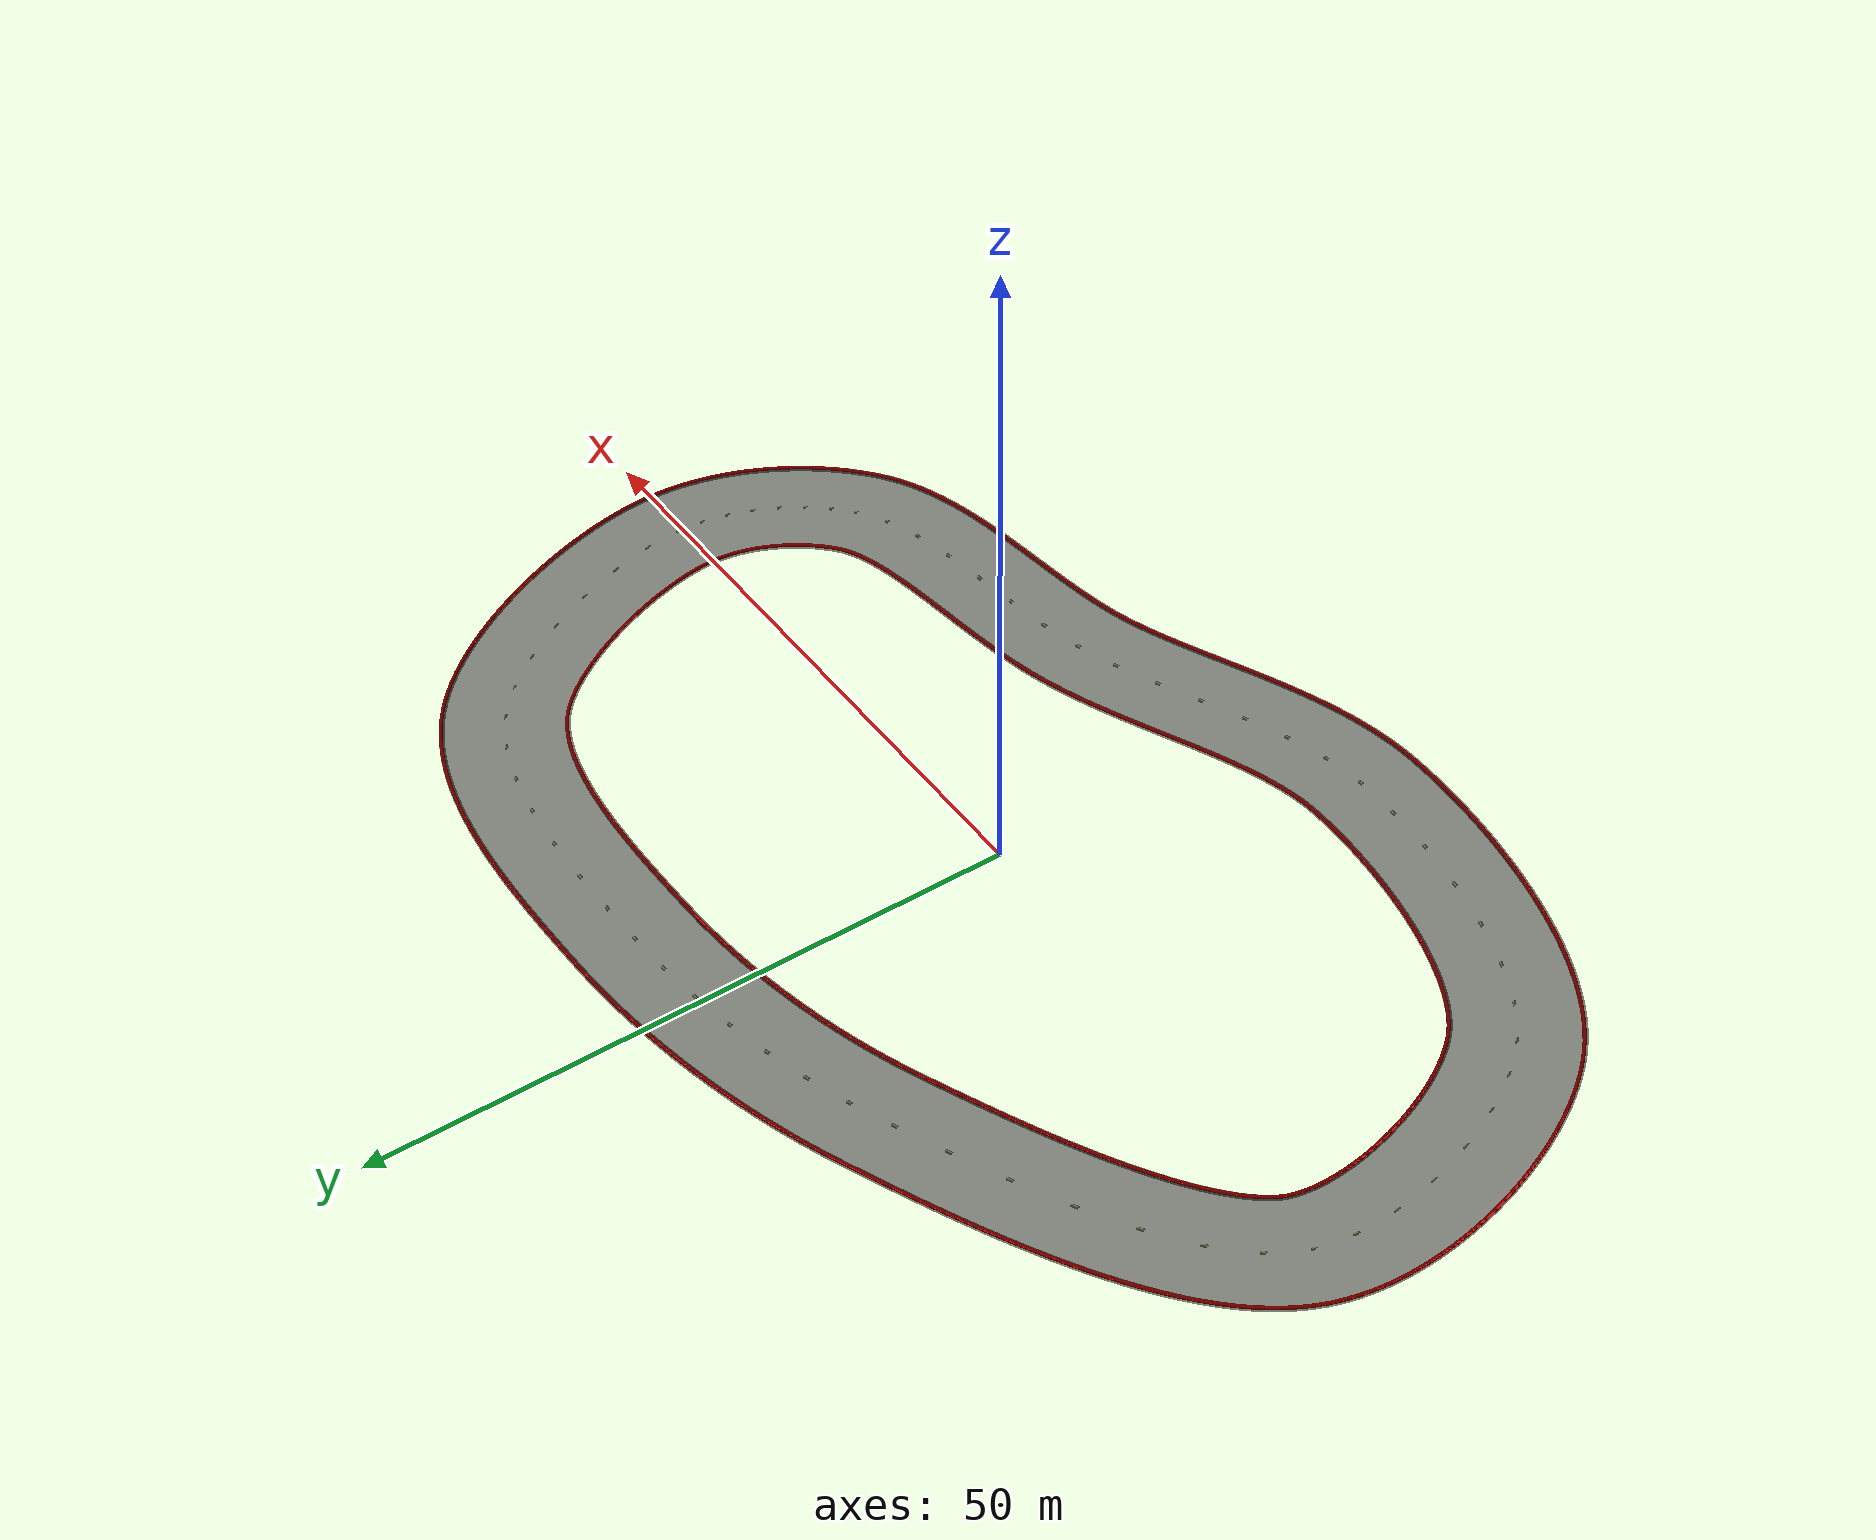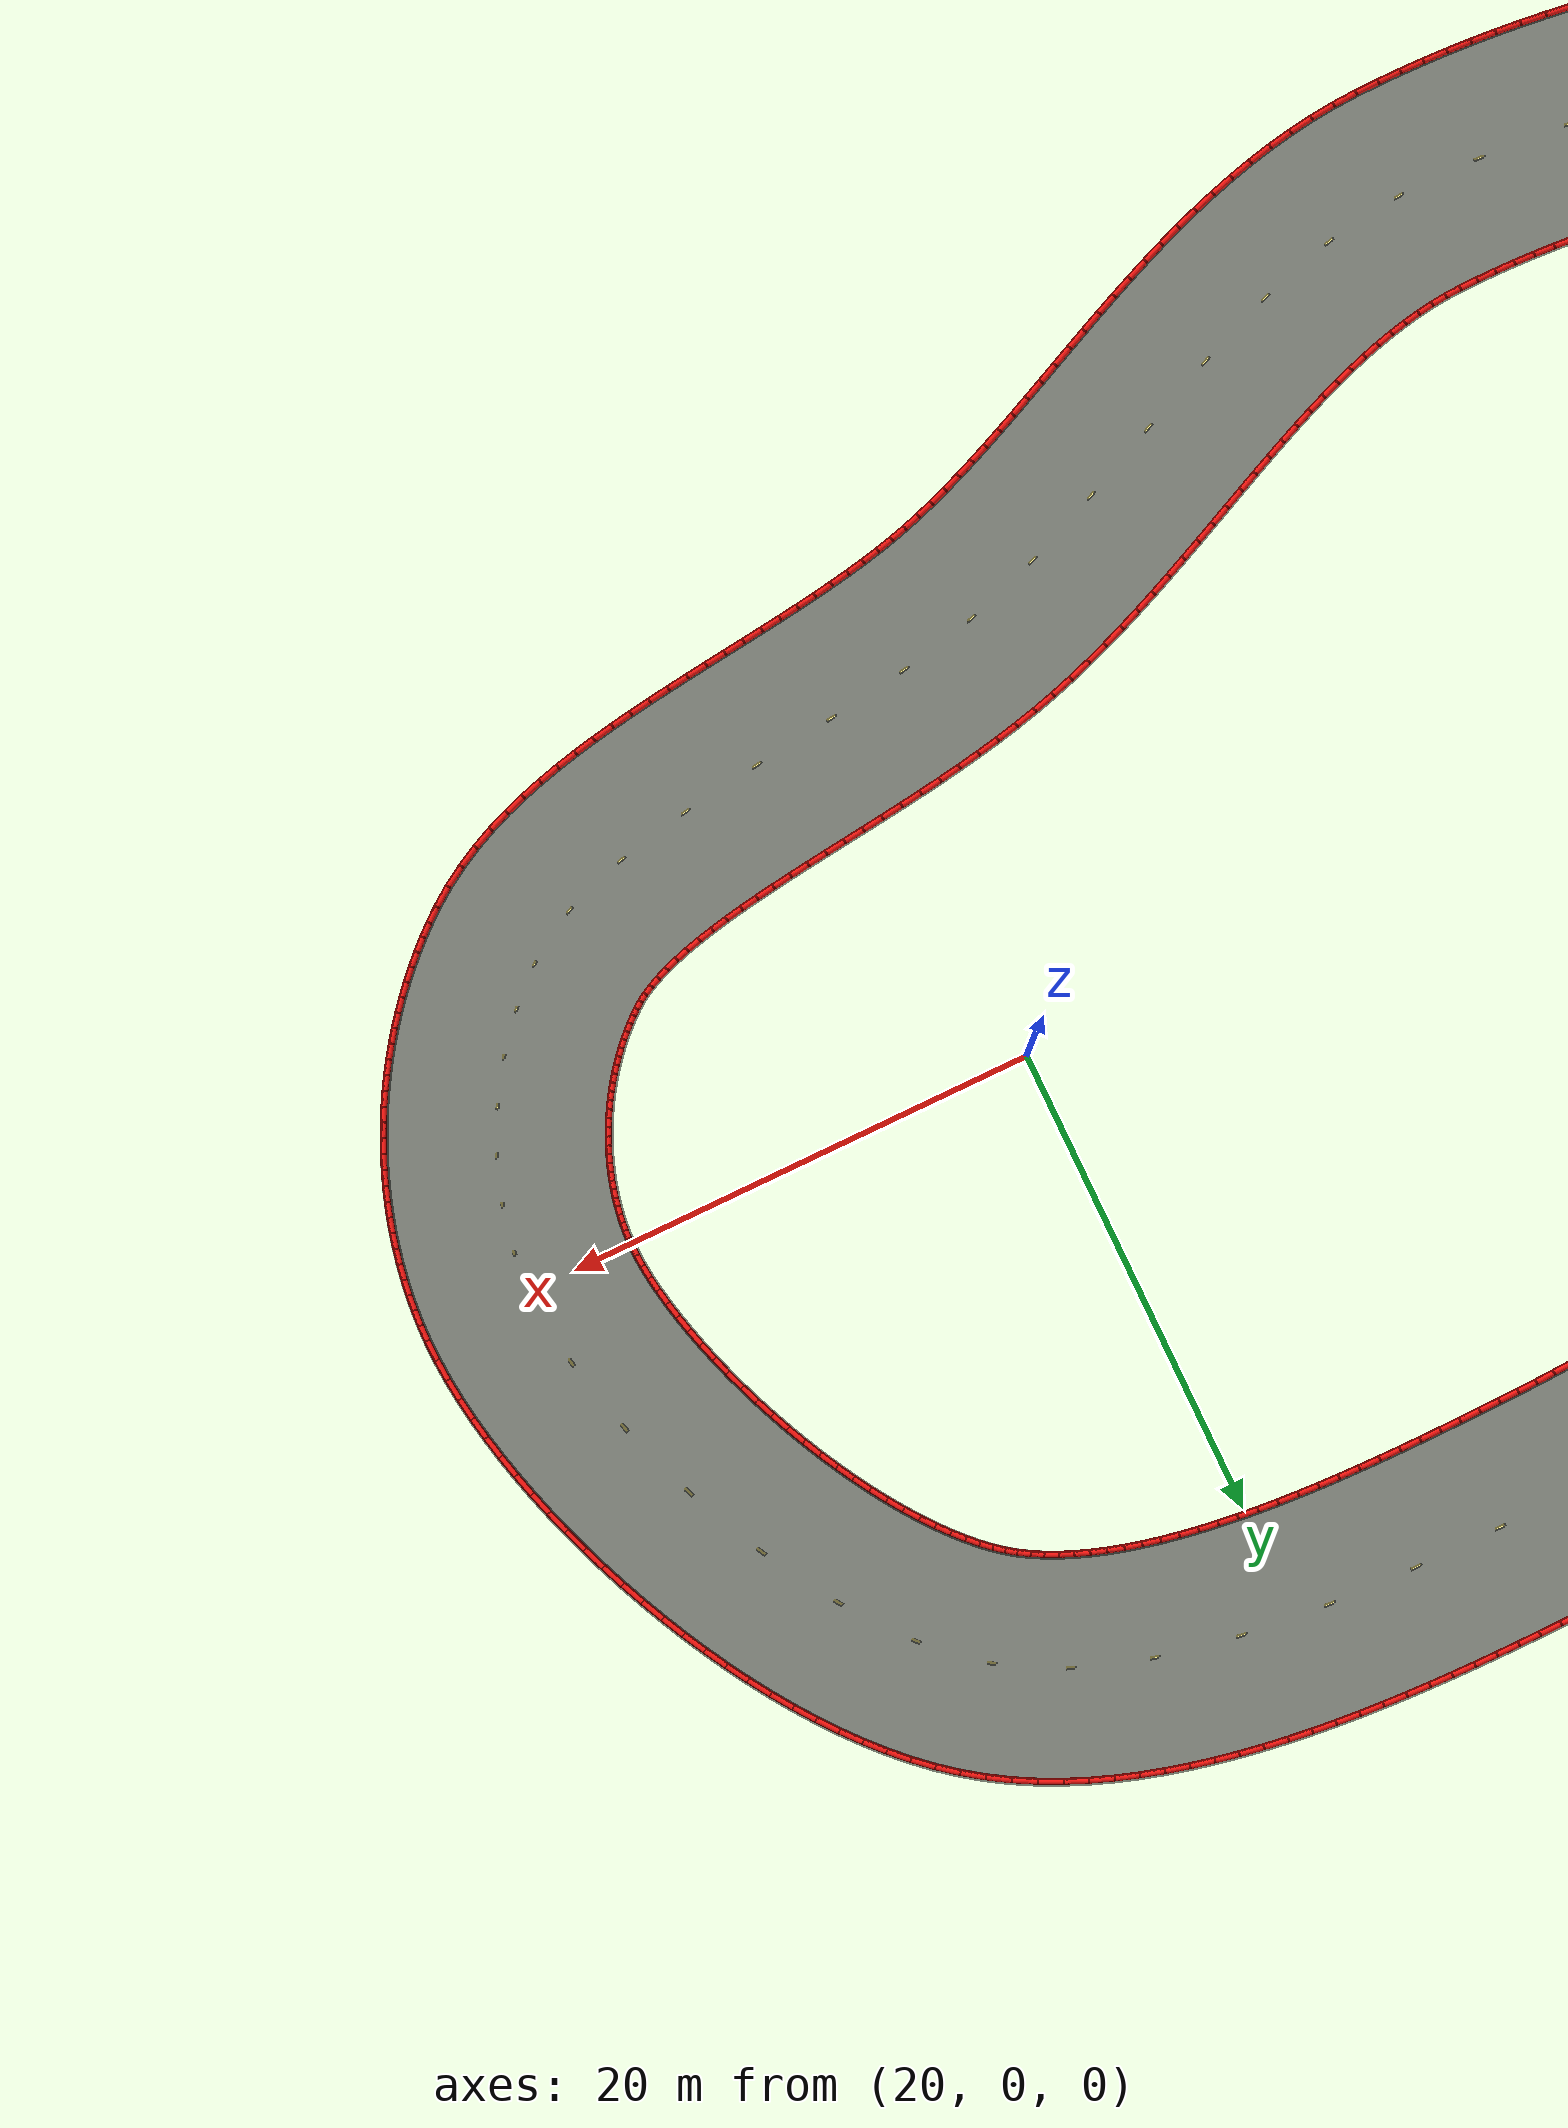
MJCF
<mujoco model="s_curve_track_visuals">
  <asset>
    <mesh name="track_surface_mesh" inertia="shell" vertex="37.50007 0.02447 0.02200 37.49263 0.47903 0.02200 37.46042 0.97197 0.02200 37.40149 1.51819 0.02200 37.31483 2.11018 0.02200 37.20014 2.74126 0.02200 37.05760 3.40543 0.02200 36.88771 4.09722 0.02200 36.69120 4.81155 0.02200 36.46896 5.54367 0.02200 36.22198 6.28907 0.02200 35.95135 7.04342 0.02200 35.65826 7.80254 0.02200 35.34394 8.56237 0.02200 35.00971 9.31890 0.02200 34.65698 10.06820 0.02200 34.28722 10.80637 0.02200 33.90203 11.52953 0.02200 33.50311 12.23382 0.02200 33.09232 12.91537 0.02200 32.67169 13.57032 0.02200 32.24348 14.19480 0.02200 31.81020 14.78498 0.02200 31.37470 15.33703 0.02200 30.94021 15.84725 0.02200 30.51045 16.31205 0.02200 30.08968 16.72816 0.02200 29.68275 17.09273 0.02200 29.29473 17.40396 0.02200 28.88897 17.69028 0.02200 28.44760 17.96387 0.02200 27.96507 18.22745 0.02200 27.44172 18.47969 0.02200 26.87859 18.71931 0.02200 26.27721 18.94515 0.02200 25.63951 19.15629 0.02200 24.96769 19.35203 0.02200 24.26413 19.53194 0.02200 23.53130 19.69581 0.02200 22.77174 19.84363 0.02200 21.98799 19.97562 0.02200 21.18260 20.09210 0.02200 20.35805 20.19359 0.02200 19.51683 20.28067 0.02200 18.66133 20.35406 0.02200 17.79393 20.41453 0.02200 16.91694 20.46294 0.02200 16.03262 20.50020 0.02200 15.14317 20.52725 0.02200 14.25074 20.54509 0.02200 13.35744 20.55474 0.02200 12.46531 20.55725 0.02200 11.57634 20.55370 0.02200 10.69245 20.54516 0.02200 9.81551 20.53276 0.02200 8.94731 20.51763 0.02200 8.10365 20.50119 0.02200 7.28873 20.47960 0.02200 6.48503 20.44789 0.02200 5.67970 20.40572 0.02200 4.87300 20.35306 0.02200 4.06517 20.28986 0.02200 3.25646 20.21609 0.02200 2.44713 20.13169 0.02200 1.63742 20.03665 0.02200 0.82757 19.93092 0.02200 0.01785 19.81446 0.02200 -0.79152 19.68724 0.02200 -1.60028 19.54923 0.02200 -2.40819 19.40039 0.02200 -3.21500 19.24070 0.02200 -4.02047 19.07012 0.02200 -4.82436 18.88862 0.02200 -5.62643 18.69617 0.02200 -6.42644 18.49276 0.02200 -7.22415 18.27834 0.02200 -8.01932 18.05290 0.02200 -8.81172 17.81640 0.02200 -9.60111 17.56883 0.02200 -10.38725 17.31016 0.02200 -11.16991 17.04036 0.02200 -11.94887 16.75942 0.02200 -12.72390 16.46731 0.02200 -13.49475 16.16401 0.02200 -14.27490 15.84380 0.02200 -15.16555 15.46986 0.02200 -16.09764 15.07599 0.02200 -17.05282 14.66839 0.02200 -18.02717 14.24726 0.02200 -19.01666 13.81288 0.02200 -20.01716 13.36556 0.02200 -21.02445 12.90568 0.02200 -22.03427 12.43368 0.02200 -23.04226 11.95005 0.02200 -24.04402 11.45535 0.02200 -25.03506 10.95021 0.02200 -26.01085 10.43538 0.02200 -26.96677 9.91168 0.02200 -27.89812 9.38009 0.02200 -28.80016 8.84178 0.02200 -29.66805 8.29809 0.02200 -30.49688 7.75065 0.02200 -31.28171 7.20140 0.02200 -32.01755 6.65267 0.02200 -32.69948 6.10733 0.02200 -33.32269 5.56882 0.02200 -33.88264 5.04130 0.02200 -34.37534 4.52975 0.02200 -34.79769 4.03996 0.02200 -35.14796 3.57846 0.02200 -35.42646 3.15209 0.02200 -35.63623 2.76717 0.02200 -35.79414 2.39976 0.02200 -35.90485 2.06163 0.02200 -36.00989 1.64749 0.02200 -36.09750 1.17826 0.02200 -36.16367 0.65825 0.02200 -36.20545 0.09234 0.02200 -36.22077 -0.51432 0.02200 -36.20834 -1.15653 0.02200 -36.16746 -1.82917 0.02200 -36.09795 -2.52727 0.02200 -36.00000 -3.24599 0.02200 -35.87408 -3.98067 0.02200 -35.72094 -4.72680 0.02200 -35.54150 -5.47997 0.02200 -35.33685 -6.23592 0.02200 -35.10824 -6.99044 0.02200 -34.85702 -7.73942 0.02200 -34.58470 -8.47880 0.02200 -34.29291 -9.20452 0.02200 -33.98342 -9.91257 0.02200 -33.65817 -10.59894 0.02200 -33.31930 -11.25959 0.02200 -32.96916 -11.89050 0.02200 -32.61040 -12.48761 0.02200 -32.24603 -13.04685 0.02200 -31.87946 -13.56420 0.02200 -31.51469 -14.03569 0.02200 -31.15633 -14.45753 0.02200 -30.81646 -14.81957 0.02200 -30.44039 -15.17429 0.02200 -30.02092 -15.52317 0.02200 -29.54698 -15.87443 0.02200 -29.02036 -16.22455 0.02200 -28.44356 -16.57040 0.02200 -27.81954 -16.90924 0.02200 -27.15157 -17.23880 0.02200 -26.44307 -17.55716 0.02200 -25.69758 -17.86279 0.02200 -24.91868 -18.15441 0.02200 -24.10994 -18.43103 0.02200 -23.27489 -18.69184 0.02200 -22.41708 -18.93622 0.02200 -21.53997 -19.16369 0.02200 -20.64703 -19.37389 0.02200 -19.74166 -19.56655 0.02200 -18.82727 -19.74149 0.02200 -17.90722 -19.89860 0.02200 -16.98486 -20.03785 0.02200 -16.06355 -20.15921 0.02200 -15.14663 -20.26276 0.02200 -14.23748 -20.34858 0.02200 -13.33948 -20.41680 0.02200 -12.45607 -20.46761 0.02200 -11.59075 -20.50124 0.02200 -10.74707 -20.51796 0.02200 -9.92872 -20.51813 0.02200 -9.16843 -20.50315 0.02200 -8.50679 -20.46749 0.02200 -7.86598 -20.40288 0.02200 -7.21340 -20.30879 0.02200 -6.54844 -20.18585 0.02200 -5.87085 -20.03477 0.02200 -5.18064 -19.85648 0.02200 -4.47801 -19.65207 0.02200 -3.76330 -19.42282 0.02200 -3.03691 -19.17020 0.02200 -2.29927 -18.89583 0.02200 -1.55079 -18.60148 0.02200 -0.79186 -18.28906 0.02200 -0.02280 -17.96056 0.02200 0.75615 -17.61808 0.02200 1.54480 -17.26377 0.02200 2.34306 -16.89987 0.02200 3.15094 -16.52867 0.02200 3.96854 -16.15250 0.02200 4.79602 -15.77375 0.02200 5.63368 -15.39486 0.02200 6.48188 -15.01830 0.02200 7.34108 -14.64664 0.02200 8.21183 -14.28250 0.02200 9.09474 -13.92860 0.02200 9.99051 -13.58773 0.02200 10.89988 -13.26285 0.02200 11.82361 -12.95702 0.02200 12.76321 -12.67330 0.02200 13.68804 -12.42378 0.02200 14.62081 -12.20043 0.02200 15.55441 -12.00134 0.02200 16.48748 -11.82324 0.02200 17.41856 -11.66312 0.02200 18.34614 -11.51818 0.02200 19.26857 -11.38581 0.02200 20.18413 -11.26355 0.02200 21.09092 -11.14905 0.02200 21.98697 -11.04009 0.02200 22.87013 -10.93457 0.02200 23.73815 -10.83048 0.02200 24.58861 -10.72591 0.02200 25.41898 -10.61907 0.02200 26.22654 -10.50830 0.02200 27.00843 -10.39209 0.02200 27.76162 -10.26913 0.02200 28.48291 -10.13831 0.02200 29.16894 -9.99882 0.02200 29.81619 -9.85022 0.02200 30.42108 -9.69249 0.02200 30.97999 -9.52616 0.02200 31.48941 -9.35242 0.02200 31.94622 -9.17318 0.02200 32.34794 -8.99112 0.02200 32.69323 -8.80959 0.02200 32.98244 -8.63233 0.02200 33.26265 -8.42832 0.02200 33.48487 -8.24630 0.02200 33.74270 -8.02214 0.02200 33.99547 -7.78736 0.02200 34.24270 -7.54234 0.02200 34.48392 -7.28749 0.02200 34.71866 -7.02327 0.02200 34.94645 -6.75013 0.02200 35.16686 -6.46857 0.02200 35.37945 -6.17911 0.02200 35.58379 -5.88229 0.02200 35.77948 -5.57867 0.02200 35.96615 -5.26881 0.02200 36.14342 -4.95331 0.02200 36.31096 -4.63275 0.02200 36.46844 -4.30776 0.02200 36.61557 -3.97895 0.02200 36.75207 -3.64693 0.02200 36.87769 -3.31234 0.02200 36.99221 -2.97579 0.02200 37.09544 -2.63790 0.02200 37.18721 -2.29929 0.02200 37.26737 -1.96057 0.02200 37.33581 -1.62232 0.02200 37.39246 -1.28511 0.02200 37.43724 -0.94949 0.02200 37.47013 -0.61599 0.02200 37.49111 -0.28509 0.02200 46.49993 -0.02447 0.02200 46.48516 0.84547 0.02200 46.42724 1.74405 0.02200 46.33002 2.65015 0.02200 46.19646 3.56504 0.02200 46.02878 4.48916 0.02200 45.82871 5.42227 0.02200 45.59767 6.36363 0.02200 45.33686 7.31207 0.02200 45.04732 8.26611 0.02200 44.72997 9.22403 0.02200 44.38564 10.18392 0.02200 44.01508 11.14373 0.02200 43.61896 12.10129 0.02200 43.19790 13.05436 0.02200 42.75240 14.00065 0.02200 42.28292 14.93782 0.02200 41.78978 15.86352 0.02200 41.27320 16.77538 0.02200 40.73324 17.67103 0.02200 40.16980 18.54811 0.02200 39.58255 19.40423 0.02200 38.97088 20.23701 0.02200 38.33388 21.04403 0.02200 37.67023 21.82277 0.02200 36.97814 22.57057 0.02200 36.25528 23.28448 0.02200 35.49870 23.96111 0.02200 34.70527 24.59604 0.02200 33.85915 25.19343 0.02200 32.98117 25.73862 0.02200 32.08073 26.23127 0.02200 31.16131 26.67509 0.02200 30.22572 27.07375 0.02200 29.27624 27.43077 0.02200 28.31479 27.74948 0.02200 27.34298 28.03293 0.02200 26.36228 28.28395 0.02200 25.37404 28.50514 0.02200 24.37956 28.69885 0.02200 23.38012 28.86730 0.02200 22.37702 29.01249 0.02200 21.37159 29.13634 0.02200 20.36519 29.24060 0.02200 19.35924 29.32696 0.02200 18.35520 29.39701 0.02200 17.35460 29.45230 0.02200 16.35902 29.49428 0.02200 15.37006 29.52439 0.02200 14.38942 29.54402 0.02200 13.41882 29.55453 0.02200 12.46005 29.55725 0.02200 11.51496 29.55349 0.02200 10.58545 29.54453 0.02200 9.67349 29.53164 0.02200 8.78111 29.51609 0.02200 7.89635 29.49881 0.02200 6.99175 29.47470 0.02200 6.07228 29.43842 0.02200 5.15125 29.39019 0.02200 4.22887 29.32998 0.02200 3.30535 29.25773 0.02200 2.38093 29.17340 0.02200 1.45581 29.07693 0.02200 0.53021 28.96828 0.02200 -0.39565 28.84740 0.02200 -1.32155 28.71424 0.02200 -2.24727 28.56873 0.02200 -3.17258 28.41082 0.02200 -4.09727 28.24047 0.02200 -5.02112 28.05761 0.02200 -5.94389 27.86219 0.02200 -6.86537 27.65414 0.02200 -7.78532 27.43341 0.02200 -8.70353 27.19993 0.02200 -9.61977 26.95365 0.02200 -10.53380 26.69451 0.02200 -11.44539 26.42243 0.02200 -12.35432 26.13737 0.02200 -13.26035 25.83924 0.02200 -14.16325 25.52800 0.02200 -15.06278 25.20357 0.02200 -15.95870 24.86589 0.02200 -16.85078 24.51489 0.02200 -17.72510 24.15620 0.02200 -18.65903 23.76417 0.02200 -19.61545 23.36001 0.02200 -20.60439 22.93799 0.02200 -21.62144 22.49840 0.02200 -22.66233 22.04143 0.02200 -23.72287 21.56725 0.02200 -24.79894 21.07595 0.02200 -25.88651 20.56758 0.02200 -26.98160 20.04213 0.02200 -28.08029 19.49951 0.02200 -29.17876 18.93957 0.02200 -30.27322 18.36205 0.02200 -31.35997 17.76659 0.02200 -32.43538 17.15269 0.02200 -33.49589 16.51968 0.02200 -34.53801 15.86668 0.02200 -35.55833 15.19254 0.02200 -36.55348 14.49580 0.02200 -37.52011 13.77460 0.02200 -38.45485 13.02657 0.02200 -39.35417 12.24873 0.02200 -40.21430 11.43741 0.02200 -41.03090 10.58810 0.02200 -41.79876 9.69548 0.02200 -42.51130 8.75352 0.02200 -43.15986 7.75584 0.02200 -43.73311 6.69661 0.02200 -44.20586 5.60024 0.02200 -44.54195 4.59158 0.02200 -44.79786 3.58956 0.02200 -44.98777 2.57935 0.02200 -45.11811 1.56274 0.02200 -45.19427 0.54091 0.02200 -45.22072 -0.48520 0.02200 -45.20121 -1.51471 0.02200 -45.13882 -2.54664 0.02200 -45.03618 -3.57989 0.02200 -44.89554 -4.61322 0.02200 -44.71882 -5.64520 0.02200 -44.50771 -6.67426 0.02200 -44.26372 -7.69872 0.02200 -43.98817 -8.71677 0.02200 -43.68226 -9.72652 0.02200 -43.34703 -10.72601 0.02200 -42.98342 -11.71322 0.02200 -42.59222 -12.68611 0.02200 -42.17407 -13.64261 0.02200 -41.72947 -14.58066 0.02200 -41.25870 -15.49820 0.02200 -40.76183 -16.39319 0.02200 -40.23864 -17.26359 0.02200 -39.68854 -18.10738 0.02200 -39.11054 -18.92251 0.02200 -38.50309 -19.70687 0.02200 -37.86397 -20.45815 0.02200 -37.18354 -21.18043 0.02200 -36.40996 -21.90959 0.02200 -35.58418 -22.59779 0.02200 -34.72286 -23.23720 0.02200 -33.82978 -23.83175 0.02200 -32.90806 -24.38501 0.02200 -31.96033 -24.90010 0.02200 -30.98893 -25.37972 0.02200 -29.99601 -25.82618 0.02200 -28.98363 -26.24145 0.02200 -27.95382 -26.62719 0.02200 -26.90861 -26.98483 0.02200 -25.85004 -27.31557 0.02200 -24.78018 -27.62045 0.02200 -23.70114 -27.90036 0.02200 -22.61508 -28.15607 0.02200 -21.52416 -28.38826 0.02200 -20.43060 -28.59752 0.02200 -19.33661 -28.78437 0.02200 -18.24444 -28.94927 0.02200 -17.15634 -29.09262 0.02200 -16.07455 -29.21480 0.02200 -15.00129 -29.31611 0.02200 -13.93878 -29.39683 0.02200 -12.88916 -29.45719 0.02200 -11.85456 -29.49737 0.02200 -10.83699 -29.51751 0.02200 -9.83837 -29.51767 0.02200 -8.83157 -29.49685 0.02200 -7.81055 -29.44052 0.02200 -6.77413 -29.33640 0.02200 -5.75463 -29.18978 0.02200 -4.75235 -29.00481 0.02200 -3.76728 -28.78549 0.02200 -2.79911 -28.53567 0.02200 -1.84736 -28.25902 0.02200 -0.91140 -27.95902 0.02200 0.00946 -27.63894 0.02200 0.91593 -27.30193 0.02200 1.80871 -26.95096 0.02200 2.68847 -26.58890 0.02200 3.55581 -26.21850 0.02200 4.41128 -25.84243 0.02200 5.25534 -25.46327 0.02200 6.08836 -25.08356 0.02200 6.91062 -24.70576 0.02200 7.72232 -24.33230 0.02200 8.52357 -23.96554 0.02200 9.31437 -23.60781 0.02200 10.09463 -23.26136 0.02200 10.86418 -22.92842 0.02200 11.62277 -22.61110 0.02200 12.37006 -22.31145 0.02200 13.10565 -22.03142 0.02200 13.82907 -21.77283 0.02200 14.53986 -21.53735 0.02200 15.23679 -21.32670 0.02200 15.90764 -21.14579 0.02200 16.60647 -20.97865 0.02200 17.33603 -20.82323 0.02200 18.09335 -20.67881 0.02200 18.87551 -20.54440 0.02200 19.67968 -20.41883 0.02200 20.50316 -20.30073 0.02200 21.34332 -20.18858 0.02200 22.19770 -20.08073 0.02200 23.06394 -19.97542 0.02200 23.93981 -19.87078 0.02200 24.82323 -19.76483 0.02200 25.71224 -19.65549 0.02200 26.60506 -19.54057 0.02200 27.50003 -19.41774 0.02200 28.39566 -19.28454 0.02200 29.29064 -19.13829 0.02200 30.18381 -18.97612 0.02200 31.07418 -18.79484 0.02200 31.96091 -18.59094 0.02200 32.84325 -18.36042 0.02200 33.72046 -18.09878 0.02200 34.59167 -17.80085 0.02200 35.45569 -17.46074 0.02200 36.31063 -17.07178 0.02200 37.15347 -16.62664 0.02200 37.97952 -16.11760 0.02200 38.73735 -15.57168 0.02200 39.27523 -15.13627 0.02200 39.75813 -14.71651 0.02200 40.22611 -14.28191 0.02200 40.67906 -13.83307 0.02200 41.11685 -13.37060 0.02200 41.53936 -12.89506 0.02200 41.94645 -12.40699 0.02200 42.33796 -11.90689 0.02200 42.71373 -11.39526 0.02200 43.07359 -10.87257 0.02200 43.41733 -10.33926 0.02200 43.74475 -9.79577 0.02200 44.05561 -9.24251 0.02200 44.34966 -8.67990 0.02200 44.62661 -8.10834 0.02200 44.88617 -7.52821 0.02200 45.12801 -6.93991 0.02200 45.35178 -6.34381 0.02200 45.55712 -5.74029 0.02200 45.74360 -5.12975 0.02200 45.91082 -4.51258 0.02200 46.05830 -3.88917 0.02200 46.18557 -3.25995 0.02200 46.29210 -2.62535 0.02200 46.37737 -1.98583 0.02200 46.44081 -1.34187 0.02200 46.48182 -0.69400 0.02200" face="0 253 1 0 252 253 1 254 2 1 253 254 2 255 3 2 254 255 3 256 4 3 255 256 4 257 5 4 256 257 5 258 6 5 257 258 6 259 7 6 258 259 7 260 8 7 259 260 8 261 9 8 260 261 9 262 10 9 261 262 10 263 11 10 262 263 11 264 12 11 263 264 12 265 13 12 264 265 13 266 14 13 265 266 14 267 15 14 266 267 15 268 16 15 267 268 16 269 17 16 268 269 17 270 18 17 269 270 18 271 19 18 270 271 19 272 20 19 271 272 20 273 21 20 272 273 21 274 22 21 273 274 22 275 23 22 274 275 23 276 24 23 275 276 24 277 25 24 276 277 25 278 26 25 277 278 26 279 27 26 278 279 27 280 28 27 279 280 28 281 29 28 280 281 29 282 30 29 281 282 30 283 31 30 282 283 31 284 32 31 283 284 32 285 33 32 284 285 33 286 34 33 285 286 34 287 35 34 286 287 35 288 36 35 287 288 36 289 37 36 288 289 37 290 38 37 289 290 38 291 39 38 290 291 39 292 40 39 291 292 40 293 41 40 292 293 41 294 42 41 293 294 42 295 43 42 294 295 43 296 44 43 295 296 44 297 45 44 296 297 45 298 46 45 297 298 46 299 47 46 298 299 47 300 48 47 299 300 48 301 49 48 300 301 49 302 50 49 301 302 50 303 51 50 302 303 51 304 52 51 303 304 52 305 53 52 304 305 53 306 54 53 305 306 54 307 55 54 306 307 55 308 56 55 307 308 56 309 57 56 308 309 57 310 58 57 309 310 58 311 59 58 310 311 59 312 60 59 311 312 60 313 61 60 312 313 61 314 62 61 313 314 62 315 63 62 314 315 63 316 64 63 315 316 64 317 65 64 316 317 65 318 66 65 317 318 66 319 67 66 318 319 67 320 68 67 319 320 68 321 69 68 320 321 69 322 70 69 321 322 70 323 71 70 322 323 71 324 72 71 323 324 72 325 73 72 324 325 73 326 74 73 325 326 74 327 75 74 326 327 75 328 76 75 327 328 76 329 77 76 328 329 77 330 78 77 329 330 78 331 79 78 330 331 79 332 80 79 331 332 80 333 81 80 332 333 81 334 82 81 333 334 82 335 83 82 334 335 83 336 84 83 335 336 84 337 85 84 336 337 85 338 86 85 337 338 86 339 87 86 338 339 87 340 88 87 339 340 88 341 89 88 340 341 89 342 90 89 341 342 90 343 91 90 342 343 91 344 92 91 343 344 92 345 93 92 344 345 93 346 94 93 345 346 94 347 95 94 346 347 95 348 96 95 347 348 96 349 97 96 348 349 97 350 98 97 349 350 98 351 99 98 350 351 99 352 100 99 351 352 100 353 101 100 352 353 101 354 102 101 353 354 102 355 103 102 354 355 103 356 104 103 355 356 104 357 105 104 356 357 105 358 106 105 357 358 106 359 107 106 358 359 107 360 108 107 359 360 108 361 109 108 360 361 109 362 110 109 361 362 110 363 111 110 362 363 111 364 112 111 363 364 112 365 113 112 364 365 113 366 114 113 365 366 114 367 115 114 366 367 115 368 116 115 367 368 116 369 117 116 368 369 117 370 118 117 369 370 118 371 119 118 370 371 119 372 120 119 371 372 120 373 121 120 372 373 121 374 122 121 373 374 122 375 123 122 374 375 123 376 124 123 375 376 124 377 125 124 376 377 125 378 126 125 377 378 126 379 127 126 378 379 127 380 128 127 379 380 128 381 129 128 380 381 129 382 130 129 381 382 130 383 131 130 382 383 131 384 132 131 383 384 132 385 133 132 384 385 133 386 134 133 385 386 134 387 135 134 386 387 135 388 136 135 387 388 136 389 137 136 388 389 137 390 138 137 389 390 138 391 139 138 390 391 139 392 140 139 391 392 140 393 141 140 392 393 141 394 142 141 393 394 142 395 143 142 394 395 143 396 144 143 395 396 144 397 145 144 396 397 145 398 146 145 397 398 146 399 147 146 398 399 147 400 148 147 399 400 148 401 149 148 400 401 149 402 150 149 401 402 150 403 151 150 402 403 151 404 152 151 403 404 152 405 153 152 404 405 153 406 154 153 405 406 154 407 155 154 406 407 155 408 156 155 407 408 156 409 157 156 408 409 157 410 158 157 409 410 158 411 159 158 410 411 159 412 160 159 411 412 160 413 161 160 412 413 161 414 162 161 413 414 162 415 163 162 414 415 163 416 164 163 415 416 164 417 165 164 416 417 165 418 166 165 417 418 166 419 167 166 418 419 167 420 168 167 419 420 168 421 169 168 420 421 169 422 170 169 421 422 170 423 171 170 422 423 171 424 172 171 423 424 172 425 173 172 424 425 173 426 174 173 425 426 174 427 175 174 426 427 175 428 176 175 427 428 176 429 177 176 428 429 177 430 178 177 429 430 178 431 179 178 430 431 179 432 180 179 431 432 180 433 181 180 432 433 181 434 182 181 433 434 182 435 183 182 434 435 183 436 184 183 435 436 184 437 185 184 436 437 185 438 186 185 437 438 186 439 187 186 438 439 187 440 188 187 439 440 188 441 189 188 440 441 189 442 190 189 441 442 190 443 191 190 442 443 191 444 192 191 443 444 192 445 193 192 444 445 193 446 194 193 445 446 194 447 195 194 446 447 195 448 196 195 447 448 196 449 197 196 448 449 197 450 198 197 449 450 198 451 199 198 450 451 199 452 200 199 451 452 200 453 201 200 452 453 201 454 202 201 453 454 202 455 203 202 454 455 203 456 204 203 455 456 204 457 205 204 456 457 205 458 206 205 457 458 206 459 207 206 458 459 207 460 208 207 459 460 208 461 209 208 460 461 209 462 210 209 461 462 210 463 211 210 462 463 211 464 212 211 463 464 212 465 213 212 464 465 213 466 214 213 465 466 214 467 215 214 466 467 215 468 216 215 467 468 216 469 217 216 468 469 217 470 218 217 469 470 218 471 219 218 470 471 219 472 220 219 471 472 220 473 221 220 472 473 221 474 222 221 473 474 222 475 223 222 474 475 223 476 224 223 475 476 224 477 225 224 476 477 225 478 226 225 477 478 226 479 227 226 478 479 227 480 228 227 479 480 228 481 229 228 480 481 229 482 230 229 481 482 230 483 231 230 482 483 231 484 232 231 483 484 232 485 233 232 484 485 233 486 234 233 485 486 234 487 235 234 486 487 235 488 236 235 487 488 236 489 237 236 488 489 237 490 238 237 489 490 238 491 239 238 490 491 239 492 240 239 491 492 240 493 241 240 492 493 241 494 242 241 493 494 242 495 243 242 494 495 243 496 244 243 495 496 244 497 245 244 496 497 245 498 246 245 497 498 246 499 247 246 498 499 247 500 248 247 499 500 248 501 249 248 500 501 249 502 250 249 501 502 250 503 251 250 502 503 251 252 0 251 503 252"/>
    <material name="track_asphalt" rgba="0.48 0.49 0.46 1" emission="0.08"/>
    <material name="track_boundary" rgba="0.95 0.08 0.06 1" emission="0.05"/>
    <material name="track_centerline" rgba="1.0 0.95 0.55 1" emission="0.15"/>
  </asset>
  <worldbody>
    <geom name="track_surface" type="mesh" mesh="track_surface_mesh" material="track_asphalt" contype="0" conaffinity="0"/>
    <geom name="track_left_boundary_000" type="capsule" fromto="37.50007 0.02447 0.09 37.49263 0.47903 0.09" size="0.14" material="track_boundary" contype="0" conaffinity="0"/>
    <geom name="track_left_boundary_001" type="capsule" fromto="37.49263 0.47903 0.09 37.46042 0.97197 0.09" size="0.14" material="track_boundary" contype="0" conaffinity="0"/>
    <geom name="track_left_boundary_002" type="capsule" fromto="37.46042 0.97197 0.09 37.40149 1.51819 0.09" size="0.14" material="track_boundary" contype="0" conaffinity="0"/>
    <geom name="track_left_boundary_003" type="capsule" fromto="37.40149 1.51819 0.09 37.31483 2.11018 0.09" size="0.14" material="track_boundary" contype="0" conaffinity="0"/>
    <geom name="track_left_boundary_004" type="capsule" fromto="37.31483 2.11018 0.09 37.20014 2.74126 0.09" size="0.14" material="track_boundary" contype="0" conaffinity="0"/>
    <geom name="track_left_boundary_005" type="capsule" fromto="37.20014 2.74126 0.09 37.05760 3.40543 0.09" size="0.14" material="track_boundary" contype="0" conaffinity="0"/>
    <geom name="track_left_boundary_006" type="capsule" fromto="37.05760 3.40543 0.09 36.88771 4.09722 0.09" size="0.14" material="track_boundary" contype="0" conaffinity="0"/>
    <geom name="track_left_boundary_007" type="capsule" fromto="36.88771 4.09722 0.09 36.69120 4.81155 0.09" size="0.14" material="track_boundary" contype="0" conaffinity="0"/>
    <geom name="track_left_boundary_008" type="capsule" fromto="36.69120 4.81155 0.09 36.46896 5.54367 0.09" size="0.14" material="track_boundary" contype="0" conaffinity="0"/>
    <geom name="track_left_boundary_009" type="capsule" fromto="36.46896 5.54367 0.09 36.22198 6.28907 0.09" size="0.14" material="track_boundary" contype="0" conaffinity="0"/>
    <geom name="track_left_boundary_010" type="capsule" fromto="36.22198 6.28907 0.09 35.95135 7.04342 0.09" size="0.14" material="track_boundary" contype="0" conaffinity="0"/>
    <geom name="track_left_boundary_011" type="capsule" fromto="35.95135 7.04342 0.09 35.65826 7.80254 0.09" size="0.14" material="track_boundary" contype="0" conaffinity="0"/>
    <geom name="track_left_boundary_012" type="capsule" fromto="35.65826 7.80254 0.09 35.34394 8.56237 0.09" size="0.14" material="track_boundary" contype="0" conaffinity="0"/>
    <geom name="track_left_boundary_013" type="capsule" fromto="35.34394 8.56237 0.09 35.00971 9.31890 0.09" size="0.14" material="track_boundary" contype="0" conaffinity="0"/>
    <geom name="track_left_boundary_014" type="capsule" fromto="35.00971 9.31890 0.09 34.65698 10.06820 0.09" size="0.14" material="track_boundary" contype="0" conaffinity="0"/>
    <geom name="track_left_boundary_015" type="capsule" fromto="34.65698 10.06820 0.09 34.28722 10.80637 0.09" size="0.14" material="track_boundary" contype="0" conaffinity="0"/>
    <geom name="track_left_boundary_016" type="capsule" fromto="34.28722 10.80637 0.09 33.90203 11.52953 0.09" size="0.14" material="track_boundary" contype="0" conaffinity="0"/>
    <geom name="track_left_boundary_017" type="capsule" fromto="33.90203 11.52953 0.09 33.50311 12.23382 0.09" size="0.14" material="track_boundary" contype="0" conaffinity="0"/>
    <geom name="track_left_boundary_018" type="capsule" fromto="33.50311 12.23382 0.09 33.09232 12.91537 0.09" size="0.14" material="track_boundary" contype="0" conaffinity="0"/>
    <geom name="track_left_boundary_019" type="capsule" fromto="33.09232 12.91537 0.09 32.67169 13.57032 0.09" size="0.14" material="track_boundary" contype="0" conaffinity="0"/>
    <geom name="track_left_boundary_020" type="capsule" fromto="32.67169 13.57032 0.09 32.24348 14.19480 0.09" size="0.14" material="track_boundary" contype="0" conaffinity="0"/>
    <geom name="track_left_boundary_021" type="capsule" fromto="32.24348 14.19480 0.09 31.81020 14.78498 0.09" size="0.14" material="track_boundary" contype="0" conaffinity="0"/>
    <geom name="track_left_boundary_022" type="capsule" fromto="31.81020 14.78498 0.09 31.37470 15.33703 0.09" size="0.14" material="track_boundary" contype="0" conaffinity="0"/>
    <geom name="track_left_boundary_023" type="capsule" fromto="31.37470 15.33703 0.09 30.94021 15.84725 0.09" size="0.14" material="track_boundary" contype="0" conaffinity="0"/>
    <geom name="track_left_boundary_024" type="capsule" fromto="30.94021 15.84725 0.09 30.51045 16.31205 0.09" size="0.14" material="track_boundary" contype="0" conaffinity="0"/>
    <geom name="track_left_boundary_025" type="capsule" fromto="30.51045 16.31205 0.09 30.08968 16.72816 0.09" size="0.14" material="track_boundary" contype="0" conaffinity="0"/>
    <geom name="track_left_boundary_026" type="capsule" fromto="30.08968 16.72816 0.09 29.68275 17.09273 0.09" size="0.14" material="track_boundary" contype="0" conaffinity="0"/>
    <geom name="track_left_boundary_027" type="capsule" fromto="29.68275 17.09273 0.09 29.29473 17.40396 0.09" size="0.14" material="track_boundary" contype="0" conaffinity="0"/>
    <geom name="track_left_boundary_028" type="capsule" fromto="29.29473 17.40396 0.09 28.88897 17.69028 0.09" size="0.14" material="track_boundary" contype="0" conaffinity="0"/>
    <geom name="track_left_boundary_029" type="capsule" fromto="28.88897 17.69028 0.09 28.44760 17.96387 0.09" size="0.14" material="track_boundary" contype="0" conaffinity="0"/>
    <geom name="track_left_boundary_030" type="capsule" fromto="28.44760 17.96387 0.09 27.96507 18.22745 0.09" size="0.14" material="track_boundary" contype="0" conaffinity="0"/>
    <geom name="track_left_boundary_031" type="capsule" fromto="27.96507 18.22745 0.09 27.44172 18.47969 0.09" size="0.14" material="track_boundary" contype="0" conaffinity="0"/>
    <geom name="track_left_boundary_032" type="capsule" fromto="27.44172 18.47969 0.09 26.87859 18.71931 0.09" size="0.14" material="track_boundary" contype="0" conaffinity="0"/>
    <geom name="track_left_boundary_033" type="capsule" fromto="26.87859 18.71931 0.09 26.27721 18.94515 0.09" size="0.14" material="track_boundary" contype="0" conaffinity="0"/>
    <geom name="track_left_boundary_034" type="capsule" fromto="26.27721 18.94515 0.09 25.63951 19.15629 0.09" size="0.14" material="track_boundary" contype="0" conaffinity="0"/>
    <geom name="track_left_boundary_035" type="capsule" fromto="25.63951 19.15629 0.09 24.96769 19.35203 0.09" size="0.14" material="track_boundary" contype="0" conaffinity="0"/>
    <geom name="track_left_boundary_036" type="capsule" fromto="24.96769 19.35203 0.09 24.26413 19.53194 0.09" size="0.14" material="track_boundary" contype="0" conaffinity="0"/>
    <geom name="track_left_boundary_037" type="capsule" fromto="24.26413 19.53194 0.09 23.53130 19.69581 0.09" size="0.14" material="track_boundary" contype="0" conaffinity="0"/>
    <geom name="track_left_boundary_038" type="capsule" fromto="23.53130 19.69581 0.09 22.77174 19.84363 0.09" size="0.14" material="track_boundary" contype="0" conaffinity="0"/>
    <geom name="track_left_boundary_039" type="capsule" fromto="22.77174 19.84363 0.09 21.98799 19.97562 0.09" size="0.14" material="track_boundary" contype="0" conaffinity="0"/>
    <geom name="track_left_boundary_040" type="capsule" fromto="21.98799 19.97562 0.09 21.18260 20.09210 0.09" size="0.14" material="track_boundary" contype="0" conaffinity="0"/>
    <geom name="track_left_boundary_041" type="capsule" fromto="21.18260 20.09210 0.09 20.35805 20.19359 0.09" size="0.14" material="track_boundary" contype="0" conaffinity="0"/>
    <geom name="track_left_boundary_042" type="capsule" fromto="20.35805 20.19359 0.09 19.51683 20.28067 0.09" size="0.14" material="track_boundary" contype="0" conaffinity="0"/>
    <geom name="track_left_boundary_043" type="capsule" fromto="19.51683 20.28067 0.09 18.66133 20.35406 0.09" size="0.14" material="track_boundary" contype="0" conaffinity="0"/>
    <geom name="track_left_boundary_044" type="capsule" fromto="18.66133 20.35406 0.09 17.79393 20.41453 0.09" size="0.14" material="track_boundary" contype="0" conaffinity="0"/>
    <geom name="track_left_boundary_045" type="capsule" fromto="17.79393 20.41453 0.09 16.91694 20.46294 0.09" size="0.14" material="track_boundary" contype="0" conaffinity="0"/>
    <geom name="track_left_boundary_046" type="capsule" fromto="16.91694 20.46294 0.09 16.03262 20.50020 0.09" size="0.14" material="track_boundary" contype="0" conaffinity="0"/>
    <geom name="track_left_boundary_047" type="capsule" fromto="16.03262 20.50020 0.09 15.14317 20.52725 0.09" size="0.14" material="track_boundary" contype="0" conaffinity="0"/>
    <geom name="track_left_boundary_048" type="capsule" fromto="15.14317 20.52725 0.09 14.25074 20.54509 0.09" size="0.14" material="track_boundary" contype="0" conaffinity="0"/>
    <geom name="track_left_boundary_049" type="capsule" fromto="14.25074 20.54509 0.09 13.35744 20.55474 0.09" size="0.14" material="track_boundary" contype="0" conaffinity="0"/>
    <geom name="track_left_boundary_050" type="capsule" fromto="13.35744 20.55474 0.09 12.46531 20.55725 0.09" size="0.14" material="track_boundary" contype="0" conaffinity="0"/>
    <geom name="track_left_boundary_051" type="capsule" fromto="12.46531 20.55725 0.09 11.57634 20.55370 0.09" size="0.14" material="track_boundary" contype="0" conaffinity="0"/>
    <geom name="track_left_boundary_052" type="capsule" fromto="11.57634 20.55370 0.09 10.69245 20.54516 0.09" size="0.14" material="track_boundary" contype="0" conaffinity="0"/>
    <geom name="track_left_boundary_053" type="capsule" fromto="10.69245 20.54516 0.09 9.81551 20.53276 0.09" size="0.14" material="track_boundary" contype="0" conaffinity="0"/>
    <geom name="track_left_boundary_054" type="capsule" fromto="9.81551 20.53276 0.09 8.94731 20.51763 0.09" size="0.14" material="track_boundary" contype="0" conaffinity="0"/>
    <geom name="track_left_boundary_055" type="capsule" fromto="8.94731 20.51763 0.09 8.10365 20.50119 0.09" size="0.14" material="track_boundary" contype="0" conaffinity="0"/>
    <geom name="track_left_boundary_056" type="capsule" fromto="8.10365 20.50119 0.09 7.28873 20.47960 0.09" size="0.14" material="track_boundary" contype="0" conaffinity="0"/>
    <geom name="track_left_boundary_057" type="capsule" fromto="7.28873 20.47960 0.09 6.48503 20.44789 0.09" size="0.14" material="track_boundary" contype="0" conaffinity="0"/>
    <geom name="track_left_boundary_058" type="capsule" fromto="6.48503 20.44789 0.09 5.67970 20.40572 0.09" size="0.14" material="track_boundary" contype="0" conaffinity="0"/>
    <geom name="track_left_boundary_059" type="capsule" fromto="5.67970 20.40572 0.09 4.87300 20.35306 0.09" size="0.14" material="track_boundary" contype="0" conaffinity="0"/>
    <geom name="track_left_boundary_060" type="capsule" fromto="4.87300 20.35306 0.09 4.06517 20.28986 0.09" size="0.14" material="track_boundary" contype="0" conaffinity="0"/>
    <geom name="track_left_boundary_061" type="capsule" fromto="4.06517 20.28986 0.09 3.25646 20.21609 0.09" size="0.14" material="track_boundary" contype="0" conaffinity="0"/>
    <geom name="track_left_boundary_062" type="capsule" fromto="3.25646 20.21609 0.09 2.44713 20.13169 0.09" size="0.14" material="track_boundary" contype="0" conaffinity="0"/>
    <geom name="track_left_boundary_063" type="capsule" fromto="2.44713 20.13169 0.09 1.63742 20.03665 0.09" size="0.14" material="track_boundary" contype="0" conaffinity="0"/>
    <geom name="track_left_boundary_064" type="capsule" fromto="1.63742 20.03665 0.09 0.82757 19.93092 0.09" size="0.14" material="track_boundary" contype="0" conaffinity="0"/>
    <geom name="track_left_boundary_065" type="capsule" fromto="0.82757 19.93092 0.09 0.01785 19.81446 0.09" size="0.14" material="track_boundary" contype="0" conaffinity="0"/>
    <geom name="track_left_boundary_066" type="capsule" fromto="0.01785 19.81446 0.09 -0.79152 19.68724 0.09" size="0.14" material="track_boundary" contype="0" conaffinity="0"/>
    <geom name="track_left_boundary_067" type="capsule" fromto="-0.79152 19.68724 0.09 -1.60028 19.54923 0.09" size="0.14" material="track_boundary" contype="0" conaffinity="0"/>
    <geom name="track_left_boundary_068" type="capsule" fromto="-1.60028 19.54923 0.09 -2.40819 19.40039 0.09" size="0.14" material="track_boundary" contype="0" conaffinity="0"/>
    <geom name="track_left_boundary_069" type="capsule" fromto="-2.40819 19.40039 0.09 -3.21500 19.24070 0.09" size="0.14" material="track_boundary" contype="0" conaffinity="0"/>
    <geom name="track_left_boundary_070" type="capsule" fromto="-3.21500 19.24070 0.09 -4.02047 19.07012 0.09" size="0.14" material="track_boundary" contype="0" conaffinity="0"/>
    <geom name="track_left_boundary_071" type="capsule" fromto="-4.02047 19.07012 0.09 -4.82436 18.88862 0.09" size="0.14" material="track_boundary" contype="0" conaffinity="0"/>
    <geom name="track_left_boundary_072" type="capsule" fromto="-4.82436 18.88862 0.09 -5.62643 18.69617 0.09" size="0.14" material="track_boundary" contype="0" conaffinity="0"/>
    <geom name="track_left_boundary_073" type="capsule" fromto="-5.62643 18.69617 0.09 -6.42644 18.49276 0.09" size="0.14" material="track_boundary" contype="0" conaffinity="0"/>
    <geom name="track_left_boundary_074" type="capsule" fromto="-6.42644 18.49276 0.09 -7.22415 18.27834 0.09" size="0.14" material="track_boundary" contype="0" conaffinity="0"/>
    <geom name="track_left_boundary_075" type="capsule" fromto="-7.22415 18.27834 0.09 -8.01932 18.05290 0.09" size="0.14" material="track_boundary" contype="0" conaffinity="0"/>
    <geom name="track_left_boundary_076" type="capsule" fromto="-8.01932 18.05290 0.09 -8.81172 17.81640 0.09" size="0.14" material="track_boundary" contype="0" conaffinity="0"/>
    <geom name="track_left_boundary_077" type="capsule" fromto="-8.81172 17.81640 0.09 -9.60111 17.56883 0.09" size="0.14" material="track_boundary" contype="0" conaffinity="0"/>
    <geom name="track_left_boundary_078" type="capsule" fromto="-9.60111 17.56883 0.09 -10.38725 17.31016 0.09" size="0.14" material="track_boundary" contype="0" conaffinity="0"/>
    <geom name="track_left_boundary_079" type="capsule" fromto="-10.38725 17.31016 0.09 -11.16991 17.04036 0.09" size="0.14" material="track_boundary" contype="0" conaffinity="0"/>
    <geom name="track_left_boundary_080" type="capsule" fromto="-11.16991 17.04036 0.09 -11.94887 16.75942 0.09" size="0.14" material="track_boundary" contype="0" conaffinity="0"/>
    <geom name="track_left_boundary_081" type="capsule" fromto="-11.94887 16.75942 0.09 -12.72390 16.46731 0.09" size="0.14" material="track_boundary" contype="0" conaffinity="0"/>
    <geom name="track_left_boundary_082" type="capsule" fromto="-12.72390 16.46731 0.09 -13.49475 16.16401 0.09" size="0.14" material="track_boundary" contype="0" conaffinity="0"/>
    <geom name="track_left_boundary_083" type="capsule" fromto="-13.49475 16.16401 0.09 -14.27490 15.84380 0.09" size="0.14" material="track_boundary" contype="0" conaffinity="0"/>
    <geom name="track_left_boundary_084" type="capsule" fromto="-14.27490 15.84380 0.09 -15.16555 15.46986 0.09" size="0.14" material="track_boundary" contype="0" conaffinity="0"/>
    <geom name="track_left_boundary_085" type="capsule" fromto="-15.16555 15.46986 0.09 -16.09764 15.07599 0.09" size="0.14" material="track_boundary" contype="0" conaffinity="0"/>
    <geom name="track_left_boundary_086" type="capsule" fromto="-16.09764 15.07599 0.09 -17.05282 14.66839 0.09" size="0.14" material="track_boundary" contype="0" conaffinity="0"/>
    <geom name="track_left_boundary_087" type="capsule" fromto="-17.05282 14.66839 0.09 -18.02717 14.24726 0.09" size="0.14" material="track_boundary" contype="0" conaffinity="0"/>
    <geom name="track_left_boundary_088" type="capsule" fromto="-18.02717 14.24726 0.09 -19.01666 13.81288 0.09" size="0.14" material="track_boundary" contype="0" conaffinity="0"/>
    <geom name="track_left_boundary_089" type="capsule" fromto="-19.01666 13.81288 0.09 -20.01716 13.36556 0.09" size="0.14" material="track_boundary" contype="0" conaffinity="0"/>
    <geom name="track_left_boundary_090" type="capsule" fromto="-20.01716 13.36556 0.09 -21.02445 12.90568 0.09" size="0.14" material="track_boundary" contype="0" conaffinity="0"/>
    <geom name="track_left_boundary_091" type="capsule" fromto="-21.02445 12.90568 0.09 -22.03427 12.43368 0.09" size="0.14" material="track_boundary" contype="0" conaffinity="0"/>
    <geom name="track_left_boundary_092" type="capsule" fromto="-22.03427 12.43368 0.09 -23.04226 11.95005 0.09" size="0.14" material="track_boundary" contype="0" conaffinity="0"/>
    <geom name="track_left_boundary_093" type="capsule" fromto="-23.04226 11.95005 0.09 -24.04402 11.45535 0.09" size="0.14" material="track_boundary" contype="0" conaffinity="0"/>
    <geom name="track_left_boundary_094" type="capsule" fromto="-24.04402 11.45535 0.09 -25.03506 10.95021 0.09" size="0.14" material="track_boundary" contype="0" conaffinity="0"/>
    <geom name="track_left_boundary_095" type="capsule" fromto="-25.03506 10.95021 0.09 -26.01085 10.43538 0.09" size="0.14" material="track_boundary" contype="0" conaffinity="0"/>
    <geom name="track_left_boundary_096" type="capsule" fromto="-26.01085 10.43538 0.09 -26.96677 9.91168 0.09" size="0.14" material="track_boundary" contype="0" conaffinity="0"/>
    <geom name="track_left_boundary_097" type="capsule" fromto="-26.96677 9.91168 0.09 -27.89812 9.38009 0.09" size="0.14" material="track_boundary" contype="0" conaffinity="0"/>
    <geom name="track_left_boundary_098" type="capsule" fromto="-27.89812 9.38009 0.09 -28.80016 8.84178 0.09" size="0.14" material="track_boundary" contype="0" conaffinity="0"/>
    <geom name="track_left_boundary_099" type="capsule" fromto="-28.80016 8.84178 0.09 -29.66805 8.29809 0.09" size="0.14" material="track_boundary" contype="0" conaffinity="0"/>
    <geom name="track_left_boundary_100" type="capsule" fromto="-29.66805 8.29809 0.09 -30.49688 7.75065 0.09" size="0.14" material="track_boundary" contype="0" conaffinity="0"/>
    <geom name="track_left_boundary_101" type="capsule" fromto="-30.49688 7.75065 0.09 -31.28171 7.20140 0.09" size="0.14" material="track_boundary" contype="0" conaffinity="0"/>
    <geom name="track_left_boundary_102" type="capsule" fromto="-31.28171 7.20140 0.09 -32.01755 6.65267 0.09" size="0.14" material="track_boundary" contype="0" conaffinity="0"/>
    <geom name="track_left_boundary_103" type="capsule" fromto="-32.01755 6.65267 0.09 -32.69948 6.10733 0.09" size="0.14" material="track_boundary" contype="0" conaffinity="0"/>
    <geom name="track_left_boundary_104" type="capsule" fromto="-32.69948 6.10733 0.09 -33.32269 5.56882 0.09" size="0.14" material="track_boundary" contype="0" conaffinity="0"/>
    <geom name="track_left_boundary_105" type="capsule" fromto="-33.32269 5.56882 0.09 -33.88264 5.04130 0.09" size="0.14" material="track_boundary" contype="0" conaffinity="0"/>
    <geom name="track_left_boundary_106" type="capsule" fromto="-33.88264 5.04130 0.09 -34.37534 4.52975 0.09" size="0.14" material="track_boundary" contype="0" conaffinity="0"/>
    <geom name="track_left_boundary_107" type="capsule" fromto="-34.37534 4.52975 0.09 -34.79769 4.03996 0.09" size="0.14" material="track_boundary" contype="0" conaffinity="0"/>
    <geom name="track_left_boundary_108" type="capsule" fromto="-34.79769 4.03996 0.09 -35.14796 3.57846 0.09" size="0.14" material="track_boundary" contype="0" conaffinity="0"/>
    <geom name="track_left_boundary_109" type="capsule" fromto="-35.14796 3.57846 0.09 -35.42646 3.15209 0.09" size="0.14" material="track_boundary" contype="0" conaffinity="0"/>
    <geom name="track_left_boundary_110" type="capsule" fromto="-35.42646 3.15209 0.09 -35.63623 2.76717 0.09" size="0.14" material="track_boundary" contype="0" conaffinity="0"/>
    <geom name="track_left_boundary_111" type="capsule" fromto="-35.63623 2.76717 0.09 -35.79414 2.39976 0.09" size="0.14" material="track_boundary" contype="0" conaffinity="0"/>
    <geom name="track_left_boundary_112" type="capsule" fromto="-35.79414 2.39976 0.09 -35.90485 2.06163 0.09" size="0.14" material="track_boundary" contype="0" conaffinity="0"/>
    <geom name="track_left_boundary_113" type="capsule" fromto="-35.90485 2.06163 0.09 -36.00989 1.64749 0.09" size="0.14" material="track_boundary" contype="0" conaffinity="0"/>
    <geom name="track_left_boundary_114" type="capsule" fromto="-36.00989 1.64749 0.09 -36.09750 1.17826 0.09" size="0.14" material="track_boundary" contype="0" conaffinity="0"/>
    <geom name="track_left_boundary_115" type="capsule" fromto="-36.09750 1.17826 0.09 -36.16367 0.65825 0.09" size="0.14" material="track_boundary" contype="0" conaffinity="0"/>
    <geom name="track_left_boundary_116" type="capsule" fromto="-36.16367 0.65825 0.09 -36.20545 0.09234 0.09" size="0.14" material="track_boundary" contype="0" conaffinity="0"/>
    <geom name="track_left_boundary_117" type="capsule" fromto="-36.20545 0.09234 0.09 -36.22077 -0.51432 0.09" size="0.14" material="track_boundary" contype="0" conaffinity="0"/>
    <geom name="track_left_boundary_118" type="capsule" fromto="-36.22077 -0.51432 0.09 -36.20834 -1.15653 0.09" size="0.14" material="track_boundary" contype="0" conaffinity="0"/>
    <geom name="track_left_boundary_119" type="capsule" fromto="-36.20834 -1.15653 0.09 -36.16746 -1.82917 0.09" size="0.14" material="track_boundary" contype="0" conaffinity="0"/>
    <geom name="track_left_boundary_120" type="capsule" fromto="-36.16746 -1.82917 0.09 -36.09795 -2.52727 0.09" size="0.14" material="track_boundary" contype="0" conaffinity="0"/>
    <geom name="track_left_boundary_121" type="capsule" fromto="-36.09795 -2.52727 0.09 -36.00000 -3.24599 0.09" size="0.14" material="track_boundary" contype="0" conaffinity="0"/>
    <geom name="track_left_boundary_122" type="capsule" fromto="-36.00000 -3.24599 0.09 -35.87408 -3.98067 0.09" size="0.14" material="track_boundary" contype="0" conaffinity="0"/>
    <geom name="track_left_boundary_123" type="capsule" fromto="-35.87408 -3.98067 0.09 -35.72094 -4.72680 0.09" size="0.14" material="track_boundary" contype="0" conaffinity="0"/>
    <geom name="track_left_boundary_124" type="capsule" fromto="-35.72094 -4.72680 0.09 -35.54150 -5.47997 0.09" size="0.14" material="track_boundary" contype="0" conaffinity="0"/>
    <geom name="track_left_boundary_125" type="capsule" fromto="-35.54150 -5.47997 0.09 -35.33685 -6.23592 0.09" size="0.14" material="track_boundary" contype="0" conaffinity="0"/>
    <geom name="track_left_boundary_126" type="capsule" fromto="-35.33685 -6.23592 0.09 -35.10824 -6.99044 0.09" size="0.14" material="track_boundary" contype="0" conaffinity="0"/>
    <geom name="track_left_boundary_127" type="capsule" fromto="-35.10824 -6.99044 0.09 -34.85702 -7.73942 0.09" size="0.14" material="track_boundary" contype="0" conaffinity="0"/>
    <geom name="track_left_boundary_128" type="capsule" fromto="-34.85702 -7.73942 0.09 -34.58470 -8.47880 0.09" size="0.14" material="track_boundary" contype="0" conaffinity="0"/>
    <geom name="track_left_boundary_129" type="capsule" fromto="-34.58470 -8.47880 0.09 -34.29291 -9.20452 0.09" size="0.14" material="track_boundary" contype="0" conaffinity="0"/>
    <geom name="track_left_boundary_130" type="capsule" fromto="-34.29291 -9.20452 0.09 -33.98342 -9.91257 0.09" size="0.14" material="track_boundary" contype="0" conaffinity="0"/>
    <geom name="track_left_boundary_131" type="capsule" fromto="-33.98342 -9.91257 0.09 -33.65817 -10.59894 0.09" size="0.14" material="track_boundary" contype="0" conaffinity="0"/>
    <geom name="track_left_boundary_132" type="capsule" fromto="-33.65817 -10.59894 0.09 -33.31930 -11.25959 0.09" size="0.14" material="track_boundary" contype="0" conaffinity="0"/>
    <geom name="track_left_boundary_133" type="capsule" fromto="-33.31930 -11.25959 0.09 -32.96916 -11.89050 0.09" size="0.14" material="track_boundary" contype="0" conaffinity="0"/>
    <geom name="track_left_boundary_134" type="capsule" fromto="-32.96916 -11.89050 0.09 -32.61040 -12.48761 0.09" size="0.14" material="track_boundary" contype="0" conaffinity="0"/>
    <geom name="track_left_boundary_135" type="capsule" fromto="-32.61040 -12.48761 0.09 -32.24603 -13.04685 0.09" size="0.14" material="track_boundary" contype="0" conaffinity="0"/>
    <geom name="track_left_boundary_136" type="capsule" fromto="-32.24603 -13.04685 0.09 -31.87946 -13.56420 0.09" size="0.14" material="track_boundary" contype="0" conaffinity="0"/>
    <geom name="track_left_boundary_137" type="capsule" fromto="-31.87946 -13.56420 0.09 -31.51469 -14.03569 0.09" size="0.14" material="track_boundary" contype="0" conaffinity="0"/>
    <geom name="track_left_boundary_138" type="capsule" fromto="-31.51469 -14.03569 0.09 -31.15633 -14.45753 0.09" size="0.14" material="track_boundary" contype="0" conaffinity="0"/>
    <geom name="track_left_boundary_139" type="capsule" fromto="-31.15633 -14.45753 0.09 -30.81646 -14.81957 0.09" size="0.14" material="track_boundary" contype="0" conaffinity="0"/>
    <geom name="track_left_boundary_140" type="capsule" fromto="-30.81646 -14.81957 0.09 -30.44039 -15.17429 0.09" size="0.14" material="track_boundary" contype="0" conaffinity="0"/>
    <geom name="track_left_boundary_141" type="capsule" fromto="-30.44039 -15.17429 0.09 -30.02092 -15.52317 0.09" size="0.14" material="track_boundary" contype="0" conaffinity="0"/>
    <geom name="track_left_boundary_142" type="capsule" fromto="-30.02092 -15.52317 0.09 -29.54698 -15.87443 0.09" size="0.14" material="track_boundary" contype="0" conaffinity="0"/>
    <geom name="track_left_boundary_143" type="capsule" fromto="-29.54698 -15.87443 0.09 -29.02036 -16.22455 0.09" size="0.14" material="track_boundary" contype="0" conaffinity="0"/>
    <geom name="track_left_boundary_144" type="capsule" fromto="-29.02036 -16.22455 0.09 -28.44356 -16.57040 0.09" size="0.14" material="track_boundary" contype="0" conaffinity="0"/>
    <geom name="track_left_boundary_145" type="capsule" fromto="-28.44356 -16.57040 0.09 -27.81954 -16.90924 0.09" size="0.14" material="track_boundary" contype="0" conaffinity="0"/>
    <geom name="track_left_boundary_146" type="capsule" fromto="-27.81954 -16.90924 0.09 -27.15157 -17.23880 0.09" size="0.14" material="track_boundary" contype="0" conaffinity="0"/>
    <geom name="track_left_boundary_147" type="capsule" fromto="-27.15157 -17.23880 0.09 -26.44307 -17.55716 0.09" size="0.14" material="track_boundary" contype="0" conaffinity="0"/>
    <geom name="track_left_boundary_148" type="capsule" fromto="-26.44307 -17.55716 0.09 -25.69758 -17.86279 0.09" size="0.14" material="track_boundary" contype="0" conaffinity="0"/>
    <geom name="track_left_boundary_149" type="capsule" fromto="-25.69758 -17.86279 0.09 -24.91868 -18.15441 0.09" size="0.14" material="track_boundary" contype="0" conaffinity="0"/>
    <geom name="track_left_boundary_150" type="capsule" fromto="-24.91868 -18.15441 0.09 -24.10994 -18.43103 0.09" size="0.14" material="track_boundary" contype="0" conaffinity="0"/>
    <geom name="track_left_boundary_151" type="capsule" fromto="-24.10994 -18.43103 0.09 -23.27489 -18.69184 0.09" size="0.14" material="track_boundary" contype="0" conaffinity="0"/>
    <geom name="track_left_boundary_152" type="capsule" fromto="-23.27489 -18.69184 0.09 -22.41708 -18.93622 0.09" size="0.14" material="track_boundary" contype="0" conaffinity="0"/>
    <geom name="track_left_boundary_153" type="capsule" fromto="-22.41708 -18.93622 0.09 -21.53997 -19.16369 0.09" size="0.14" material="track_boundary" contype="0" conaffinity="0"/>
    <geom name="track_left_boundary_154" type="capsule" fromto="-21.53997 -19.16369 0.09 -20.64703 -19.37389 0.09" size="0.14" material="track_boundary" contype="0" conaffinity="0"/>
    <geom name="track_left_boundary_155" type="capsule" fromto="-20.64703 -19.37389 0.09 -19.74166 -19.56655 0.09" size="0.14" material="track_boundary" contype="0" conaffinity="0"/>
    <geom name="track_left_boundary_156" type="capsule" fromto="-19.74166 -19.56655 0.09 -18.82727 -19.74149 0.09" size="0.14" material="track_boundary" contype="0" conaffinity="0"/>
    <geom name="track_left_boundary_157" type="capsule" fromto="-18.82727 -19.74149 0.09 -17.90722 -19.89860 0.09" size="0.14" material="track_boundary" contype="0" conaffinity="0"/>
    <geom name="track_left_boundary_158" type="capsule" fromto="-17.90722 -19.89860 0.09 -16.98486 -20.03785 0.09" size="0.14" material="track_boundary" contype="0" conaffinity="0"/>
    <geom name="track_left_boundary_159" type="capsule" fromto="-16.98486 -20.03785 0.09 -16.06355 -20.15921 0.09" size="0.14" material="track_boundary" contype="0" conaffinity="0"/>
    <geom name="track_left_boundary_160" type="capsule" fromto="-16.06355 -20.15921 0.09 -15.14663 -20.26276 0.09" size="0.14" material="track_boundary" contype="0" conaffinity="0"/>
    <geom name="track_left_boundary_161" type="capsule" fromto="-15.14663 -20.26276 0.09 -14.23748 -20.34858 0.09" size="0.14" material="track_boundary" contype="0" conaffinity="0"/>
    <geom name="track_left_boundary_162" type="capsule" fromto="-14.23748 -20.34858 0.09 -13.33948 -20.41680 0.09" size="0.14" material="track_boundary" contype="0" conaffinity="0"/>
    <geom name="track_left_boundary_163" type="capsule" fromto="-13.33948 -20.41680 0.09 -12.45607 -20.46761 0.09" size="0.14" material="track_boundary" contype="0" conaffinity="0"/>
    <geom name="track_left_boundary_164" type="capsule" fromto="-12.45607 -20.46761 0.09 -11.59075 -20.50124 0.09" size="0.14" material="track_boundary" contype="0" conaffinity="0"/>
    <geom name="track_left_boundary_165" type="capsule" fromto="-11.59075 -20.50124 0.09 -10.74707 -20.51796 0.09" size="0.14" material="track_boundary" contype="0" conaffinity="0"/>
    <geom name="track_left_boundary_166" type="capsule" fromto="-10.74707 -20.51796 0.09 -9.92872 -20.51813 0.09" size="0.14" material="track_boundary" contype="0" conaffinity="0"/>
    <geom name="track_left_boundary_167" type="capsule" fromto="-9.92872 -20.51813 0.09 -9.16843 -20.50315 0.09" size="0.14" material="track_boundary" contype="0" conaffinity="0"/>
    <geom name="track_left_boundary_168" type="capsule" fromto="-9.16843 -20.50315 0.09 -8.50679 -20.46749 0.09" size="0.14" material="track_boundary" contype="0" conaffinity="0"/>
    <geom name="track_left_boundary_169" type="capsule" fromto="-8.50679 -20.46749 0.09 -7.86598 -20.40288 0.09" size="0.14" material="track_boundary" contype="0" conaffinity="0"/>
    <geom name="track_left_boundary_170" type="capsule" fromto="-7.86598 -20.40288 0.09 -7.21340 -20.30879 0.09" size="0.14" material="track_boundary" contype="0" conaffinity="0"/>
    <geom name="track_left_boundary_171" type="capsule" fromto="-7.21340 -20.30879 0.09 -6.54844 -20.18585 0.09" size="0.14" material="track_boundary" contype="0" conaffinity="0"/>
    <geom name="track_left_boundary_172" type="capsule" fromto="-6.54844 -20.18585 0.09 -5.87085 -20.03477 0.09" size="0.14" material="track_boundary" contype="0" conaffinity="0"/>
    <geom name="track_left_boundary_173" type="capsule" fromto="-5.87085 -20.03477 0.09 -5.18064 -19.85648 0.09" size="0.14" material="track_boundary" contype="0" conaffinity="0"/>
    <geom name="track_left_boundary_174" type="capsule" fromto="-5.18064 -19.85648 0.09 -4.47801 -19.65207 0.09" size="0.14" material="track_boundary" contype="0" conaffinity="0"/>
    <geom name="track_left_boundary_175" type="capsule" fromto="-4.47801 -19.65207 0.09 -3.76330 -19.42282 0.09" size="0.14" material="track_boundary" contype="0" conaffinity="0"/>
    <geom name="track_left_boundary_176" type="capsule" fromto="-3.76330 -19.42282 0.09 -3.03691 -19.17020 0.09" size="0.14" material="track_boundary" contype="0" conaffinity="0"/>
    <geom name="track_left_boundary_177" type="capsule" fromto="-3.03691 -19.17020 0.09 -2.29927 -18.89583 0.09" size="0.14" material="track_boundary" contype="0" conaffinity="0"/>
    <geom name="track_left_boundary_178" type="capsule" fromto="-2.29927 -18.89583 0.09 -1.55079 -18.60148 0.09" size="0.14" material="track_boundary" contype="0" conaffinity="0"/>
    <geom name="track_left_boundary_179" type="capsule" fromto="-1.55079 -18.60148 0.09 -0.79186 -18.28906 0.09" size="0.14" material="track_boundary" contype="0" conaffinity="0"/>
    <geom name="track_left_boundary_180" type="capsule" fromto="-0.79186 -18.28906 0.09 -0.02280 -17.96056 0.09" size="0.14" material="track_boundary" contype="0" conaffinity="0"/>
    <geom name="track_left_boundary_181" type="capsule" fromto="-0.02280 -17.96056 0.09 0.75615 -17.61808 0.09" size="0.14" material="track_boundary" contype="0" conaffinity="0"/>
    <geom name="track_left_boundary_182" type="capsule" fromto="0.75615 -17.61808 0.09 1.54480 -17.26377 0.09" size="0.14" material="track_boundary" contype="0" conaffinity="0"/>
    <geom name="track_left_boundary_183" type="capsule" fromto="1.54480 -17.26377 0.09 2.34306 -16.89987 0.09" size="0.14" material="track_boundary" contype="0" conaffinity="0"/>
    <geom name="track_left_boundary_184" type="capsule" fromto="2.34306 -16.89987 0.09 3.15094 -16.52867 0.09" size="0.14" material="track_boundary" contype="0" conaffinity="0"/>
    <geom name="track_left_boundary_185" type="capsule" fromto="3.15094 -16.52867 0.09 3.96854 -16.15250 0.09" size="0.14" material="track_boundary" contype="0" conaffinity="0"/>
    <geom name="track_left_boundary_186" type="capsule" fromto="3.96854 -16.15250 0.09 4.79602 -15.77375 0.09" size="0.14" material="track_boundary" contype="0" conaffinity="0"/>
    <geom name="track_left_boundary_187" type="capsule" fromto="4.79602 -15.77375 0.09 5.63368 -15.39486 0.09" size="0.14" material="track_boundary" contype="0" conaffinity="0"/>
    <geom name="track_left_boundary_188" type="capsule" fromto="5.63368 -15.39486 0.09 6.48188 -15.01830 0.09" size="0.14" material="track_boundary" contype="0" conaffinity="0"/>
    <geom name="track_left_boundary_189" type="capsule" fromto="6.48188 -15.01830 0.09 7.34108 -14.64664 0.09" size="0.14" material="track_boundary" contype="0" conaffinity="0"/>
    <geom name="track_left_boundary_190" type="capsule" fromto="7.34108 -14.64664 0.09 8.21183 -14.28250 0.09" size="0.14" material="track_boundary" contype="0" conaffinity="0"/>
    <geom name="track_left_boundary_191" type="capsule" fromto="8.21183 -14.28250 0.09 9.09474 -13.92860 0.09" size="0.14" material="track_boundary" contype="0" conaffinity="0"/>
    <geom name="track_left_boundary_192" type="capsule" fromto="9.09474 -13.92860 0.09 9.99051 -13.58773 0.09" size="0.14" material="track_boundary" contype="0" conaffinity="0"/>
    <geom name="track_left_boundary_193" type="capsule" fromto="9.99051 -13.58773 0.09 10.89988 -13.26285 0.09" size="0.14" material="track_boundary" contype="0" conaffinity="0"/>
    <geom name="track_left_boundary_194" type="capsule" fromto="10.89988 -13.26285 0.09 11.82361 -12.95702 0.09" size="0.14" material="track_boundary" contype="0" conaffinity="0"/>
    <geom name="track_left_boundary_195" type="capsule" fromto="11.82361 -12.95702 0.09 12.76321 -12.67330 0.09" size="0.14" material="track_boundary" contype="0" conaffinity="0"/>
    <geom name="track_left_boundary_196" type="capsule" fromto="12.76321 -12.67330 0.09 13.68804 -12.42378 0.09" size="0.14" material="track_boundary" contype="0" conaffinity="0"/>
    <geom name="track_left_boundary_197" type="capsule" fromto="13.68804 -12.42378 0.09 14.62081 -12.20043 0.09" size="0.14" material="track_boundary" contype="0" conaffinity="0"/>
    <geom name="track_left_boundary_198" type="capsule" fromto="14.62081 -12.20043 0.09 15.55441 -12.00134 0.09" size="0.14" material="track_boundary" contype="0" conaffinity="0"/>
    <geom name="track_left_boundary_199" type="capsule" fromto="15.55441 -12.00134 0.09 16.48748 -11.82324 0.09" size="0.14" material="track_boundary" contype="0" conaffinity="0"/>
    <geom name="track_left_boundary_200" type="capsule" fromto="16.48748 -11.82324 0.09 17.41856 -11.66312 0.09" size="0.14" material="track_boundary" contype="0" conaffinity="0"/>
    <geom name="track_left_boundary_201" type="capsule" fromto="17.41856 -11.66312 0.09 18.34614 -11.51818 0.09" size="0.14" material="track_boundary" contype="0" conaffinity="0"/>
    <geom name="track_left_boundary_202" type="capsule" fromto="18.34614 -11.51818 0.09 19.26857 -11.38581 0.09" size="0.14" material="track_boundary" contype="0" conaffinity="0"/>
    <geom name="track_left_boundary_203" type="capsule" fromto="19.26857 -11.38581 0.09 20.18413 -11.26355 0.09" size="0.14" material="track_boundary" contype="0" conaffinity="0"/>
    <geom name="track_left_boundary_204" type="capsule" fromto="20.18413 -11.26355 0.09 21.09092 -11.14905 0.09" size="0.14" material="track_boundary" contype="0" conaffinity="0"/>
    <geom name="track_left_boundary_205" type="capsule" fromto="21.09092 -11.14905 0.09 21.98697 -11.04009 0.09" size="0.14" material="track_boundary" contype="0" conaffinity="0"/>
    <geom name="track_left_boundary_206" type="capsule" fromto="21.98697 -11.04009 0.09 22.87013 -10.93457 0.09" size="0.14" material="track_boundary" contype="0" conaffinity="0"/>
    <geom name="track_left_boundary_207" type="capsule" fromto="22.87013 -10.93457 0.09 23.73815 -10.83048 0.09" size="0.14" material="track_boundary" contype="0" conaffinity="0"/>
    <geom name="track_left_boundary_208" type="capsule" fromto="23.73815 -10.83048 0.09 24.58861 -10.72591 0.09" size="0.14" material="track_boundary" contype="0" conaffinity="0"/>
    <geom name="track_left_boundary_209" type="capsule" fromto="24.58861 -10.72591 0.09 25.41898 -10.61907 0.09" size="0.14" material="track_boundary" contype="0" conaffinity="0"/>
    <geom name="track_left_boundary_210" type="capsule" fromto="25.41898 -10.61907 0.09 26.22654 -10.50830 0.09" size="0.14" material="track_boundary" contype="0" conaffinity="0"/>
    <geom name="track_left_boundary_211" type="capsule" fromto="26.22654 -10.50830 0.09 27.00843 -10.39209 0.09" size="0.14" material="track_boundary" contype="0" conaffinity="0"/>
    <geom name="track_left_boundary_212" type="capsule" fromto="27.00843 -10.39209 0.09 27.76162 -10.26913 0.09" size="0.14" material="track_boundary" contype="0" conaffinity="0"/>
    <geom name="track_left_boundary_213" type="capsule" fromto="27.76162 -10.26913 0.09 28.48291 -10.13831 0.09" size="0.14" material="track_boundary" contype="0" conaffinity="0"/>
    <geom name="track_left_boundary_214" type="capsule" fromto="28.48291 -10.13831 0.09 29.16894 -9.99882 0.09" size="0.14" material="track_boundary" contype="0" conaffinity="0"/>
    <geom name="track_left_boundary_215" type="capsule" fromto="29.16894 -9.99882 0.09 29.81619 -9.85022 0.09" size="0.14" material="track_boundary" contype="0" conaffinity="0"/>
    <geom name="track_left_boundary_216" type="capsule" fromto="29.81619 -9.85022 0.09 30.42108 -9.69249 0.09" size="0.14" material="track_boundary" contype="0" conaffinity="0"/>
    <geom name="track_left_boundary_217" type="capsule" fromto="30.42108 -9.69249 0.09 30.97999 -9.52616 0.09" size="0.14" material="track_boundary" contype="0" conaffinity="0"/>
    <geom name="track_left_boundary_218" type="capsule" fromto="30.97999 -9.52616 0.09 31.48941 -9.35242 0.09" size="0.14" material="track_boundary" contype="0" conaffinity="0"/>
    <geom name="track_left_boundary_219" type="capsule" fromto="31.48941 -9.35242 0.09 31.94622 -9.17318 0.09" size="0.14" material="track_boundary" contype="0" conaffinity="0"/>
    <geom name="track_left_boundary_220" type="capsule" fromto="31.94622 -9.17318 0.09 32.34794 -8.99112 0.09" size="0.14" material="track_boundary" contype="0" conaffinity="0"/>
    <geom name="track_left_boundary_221" type="capsule" fromto="32.34794 -8.99112 0.09 32.69323 -8.80959 0.09" size="0.14" material="track_boundary" contype="0" conaffinity="0"/>
    <geom name="track_left_boundary_222" type="capsule" fromto="32.69323 -8.80959 0.09 32.98244 -8.63233 0.09" size="0.14" material="track_boundary" contype="0" conaffinity="0"/>
    <geom name="track_left_boundary_223" type="capsule" fromto="32.98244 -8.63233 0.09 33.26265 -8.42832 0.09" size="0.14" material="track_boundary" contype="0" conaffinity="0"/>
    <geom name="track_left_boundary_224" type="capsule" fromto="33.26265 -8.42832 0.09 33.48487 -8.24630 0.09" size="0.14" material="track_boundary" contype="0" conaffinity="0"/>
    <geom name="track_left_boundary_225" type="capsule" fromto="33.48487 -8.24630 0.09 33.74270 -8.02214 0.09" size="0.14" material="track_boundary" contype="0" conaffinity="0"/>
    <geom name="track_left_boundary_226" type="capsule" fromto="33.74270 -8.02214 0.09 33.99547 -7.78736 0.09" size="0.14" material="track_boundary" contype="0" conaffinity="0"/>
    <geom name="track_left_boundary_227" type="capsule" fromto="33.99547 -7.78736 0.09 34.24270 -7.54234 0.09" size="0.14" material="track_boundary" contype="0" conaffinity="0"/>
    <geom name="track_left_boundary_228" type="capsule" fromto="34.24270 -7.54234 0.09 34.48392 -7.28749 0.09" size="0.14" material="track_boundary" contype="0" conaffinity="0"/>
    <geom name="track_left_boundary_229" type="capsule" fromto="34.48392 -7.28749 0.09 34.71866 -7.02327 0.09" size="0.14" material="track_boundary" contype="0" conaffinity="0"/>
    <geom name="track_left_boundary_230" type="capsule" fromto="34.71866 -7.02327 0.09 34.94645 -6.75013 0.09" size="0.14" material="track_boundary" contype="0" conaffinity="0"/>
    <geom name="track_left_boundary_231" type="capsule" fromto="34.94645 -6.75013 0.09 35.16686 -6.46857 0.09" size="0.14" material="track_boundary" contype="0" conaffinity="0"/>
    <geom name="track_left_boundary_232" type="capsule" fromto="35.16686 -6.46857 0.09 35.37945 -6.17911 0.09" size="0.14" material="track_boundary" contype="0" conaffinity="0"/>
    <geom name="track_left_boundary_233" type="capsule" fromto="35.37945 -6.17911 0.09 35.58379 -5.88229 0.09" size="0.14" material="track_boundary" contype="0" conaffinity="0"/>
    <geom name="track_left_boundary_234" type="capsule" fromto="35.58379 -5.88229 0.09 35.77948 -5.57867 0.09" size="0.14" material="track_boundary" contype="0" conaffinity="0"/>
    <geom name="track_left_boundary_235" type="capsule" fromto="35.77948 -5.57867 0.09 35.96615 -5.26881 0.09" size="0.14" material="track_boundary" contype="0" conaffinity="0"/>
    <geom name="track_left_boundary_236" type="capsule" fromto="35.96615 -5.26881 0.09 36.14342 -4.95331 0.09" size="0.14" material="track_boundary" contype="0" conaffinity="0"/>
    <geom name="track_left_boundary_237" type="capsule" fromto="36.14342 -4.95331 0.09 36.31096 -4.63275 0.09" size="0.14" material="track_boundary" contype="0" conaffinity="0"/>
    <geom name="track_left_boundary_238" type="capsule" fromto="36.31096 -4.63275 0.09 36.46844 -4.30776 0.09" size="0.14" material="track_boundary" contype="0" conaffinity="0"/>
    <geom name="track_left_boundary_239" type="capsule" fromto="36.46844 -4.30776 0.09 36.61557 -3.97895 0.09" size="0.14" material="track_boundary" contype="0" conaffinity="0"/>
    <geom name="track_left_boundary_240" type="capsule" fromto="36.61557 -3.97895 0.09 36.75207 -3.64693 0.09" size="0.14" material="track_boundary" contype="0" conaffinity="0"/>
    <geom name="track_left_boundary_241" type="capsule" fromto="36.75207 -3.64693 0.09 36.87769 -3.31234 0.09" size="0.14" material="track_boundary" contype="0" conaffinity="0"/>
    <geom name="track_left_boundary_242" type="capsule" fromto="36.87769 -3.31234 0.09 36.99221 -2.97579 0.09" size="0.14" material="track_boundary" contype="0" conaffinity="0"/>
    <geom name="track_left_boundary_243" type="capsule" fromto="36.99221 -2.97579 0.09 37.09544 -2.63790 0.09" size="0.14" material="track_boundary" contype="0" conaffinity="0"/>
    <geom name="track_left_boundary_244" type="capsule" fromto="37.09544 -2.63790 0.09 37.18721 -2.29929 0.09" size="0.14" material="track_boundary" contype="0" conaffinity="0"/>
    <geom name="track_left_boundary_245" type="capsule" fromto="37.18721 -2.29929 0.09 37.26737 -1.96057 0.09" size="0.14" material="track_boundary" contype="0" conaffinity="0"/>
    <geom name="track_left_boundary_246" type="capsule" fromto="37.26737 -1.96057 0.09 37.33581 -1.62232 0.09" size="0.14" material="track_boundary" contype="0" conaffinity="0"/>
    <geom name="track_left_boundary_247" type="capsule" fromto="37.33581 -1.62232 0.09 37.39246 -1.28511 0.09" size="0.14" material="track_boundary" contype="0" conaffinity="0"/>
    <geom name="track_left_boundary_248" type="capsule" fromto="37.39246 -1.28511 0.09 37.43724 -0.94949 0.09" size="0.14" material="track_boundary" contype="0" conaffinity="0"/>
    <geom name="track_left_boundary_249" type="capsule" fromto="37.43724 -0.94949 0.09 37.47013 -0.61599 0.09" size="0.14" material="track_boundary" contype="0" conaffinity="0"/>
    <geom name="track_left_boundary_250" type="capsule" fromto="37.47013 -0.61599 0.09 37.49111 -0.28509 0.09" size="0.14" material="track_boundary" contype="0" conaffinity="0"/>
    <geom name="track_left_boundary_251" type="capsule" fromto="37.49111 -0.28509 0.09 37.50007 0.02447 0.09" size="0.14" material="track_boundary" contype="0" conaffinity="0"/>
    <geom name="track_right_boundary_000" type="capsule" fromto="46.49993 -0.02447 0.09 46.48516 0.84547 0.09" size="0.14" material="track_boundary" contype="0" conaffinity="0"/>
    <geom name="track_right_boundary_001" type="capsule" fromto="46.48516 0.84547 0.09 46.42724 1.74405 0.09" size="0.14" material="track_boundary" contype="0" conaffinity="0"/>
    <geom name="track_right_boundary_002" type="capsule" fromto="46.42724 1.74405 0.09 46.33002 2.65015 0.09" size="0.14" material="track_boundary" contype="0" conaffinity="0"/>
    <geom name="track_right_boundary_003" type="capsule" fromto="46.33002 2.65015 0.09 46.19646 3.56504 0.09" size="0.14" material="track_boundary" contype="0" conaffinity="0"/>
    <geom name="track_right_boundary_004" type="capsule" fromto="46.19646 3.56504 0.09 46.02878 4.48916 0.09" size="0.14" material="track_boundary" contype="0" conaffinity="0"/>
    <geom name="track_right_boundary_005" type="capsule" fromto="46.02878 4.48916 0.09 45.82871 5.42227 0.09" size="0.14" material="track_boundary" contype="0" conaffinity="0"/>
    <geom name="track_right_boundary_006" type="capsule" fromto="45.82871 5.42227 0.09 45.59767 6.36363 0.09" size="0.14" material="track_boundary" contype="0" conaffinity="0"/>
    <geom name="track_right_boundary_007" type="capsule" fromto="45.59767 6.36363 0.09 45.33686 7.31207 0.09" size="0.14" material="track_boundary" contype="0" conaffinity="0"/>
    <geom name="track_right_boundary_008" type="capsule" fromto="45.33686 7.31207 0.09 45.04732 8.26611 0.09" size="0.14" material="track_boundary" contype="0" conaffinity="0"/>
    <geom name="track_right_boundary_009" type="capsule" fromto="45.04732 8.26611 0.09 44.72997 9.22403 0.09" size="0.14" material="track_boundary" contype="0" conaffinity="0"/>
    <geom name="track_right_boundary_010" type="capsule" fromto="44.72997 9.22403 0.09 44.38564 10.18392 0.09" size="0.14" material="track_boundary" contype="0" conaffinity="0"/>
    <geom name="track_right_boundary_011" type="capsule" fromto="44.38564 10.18392 0.09 44.01508 11.14373 0.09" size="0.14" material="track_boundary" contype="0" conaffinity="0"/>
    <geom name="track_right_boundary_012" type="capsule" fromto="44.01508 11.14373 0.09 43.61896 12.10129 0.09" size="0.14" material="track_boundary" contype="0" conaffinity="0"/>
    <geom name="track_right_boundary_013" type="capsule" fromto="43.61896 12.10129 0.09 43.19790 13.05436 0.09" size="0.14" material="track_boundary" contype="0" conaffinity="0"/>
    <geom name="track_right_boundary_014" type="capsule" fromto="43.19790 13.05436 0.09 42.75240 14.00065 0.09" size="0.14" material="track_boundary" contype="0" conaffinity="0"/>
    <geom name="track_right_boundary_015" type="capsule" fromto="42.75240 14.00065 0.09 42.28292 14.93782 0.09" size="0.14" material="track_boundary" contype="0" conaffinity="0"/>
    <geom name="track_right_boundary_016" type="capsule" fromto="42.28292 14.93782 0.09 41.78978 15.86352 0.09" size="0.14" material="track_boundary" contype="0" conaffinity="0"/>
    <geom name="track_right_boundary_017" type="capsule" fromto="41.78978 15.86352 0.09 41.27320 16.77538 0.09" size="0.14" material="track_boundary" contype="0" conaffinity="0"/>
    <geom name="track_right_boundary_018" type="capsule" fromto="41.27320 16.77538 0.09 40.73324 17.67103 0.09" size="0.14" material="track_boundary" contype="0" conaffinity="0"/>
    <geom name="track_right_boundary_019" type="capsule" fromto="40.73324 17.67103 0.09 40.16980 18.54811 0.09" size="0.14" material="track_boundary" contype="0" conaffinity="0"/>
    <geom name="track_right_boundary_020" type="capsule" fromto="40.16980 18.54811 0.09 39.58255 19.40423 0.09" size="0.14" material="track_boundary" contype="0" conaffinity="0"/>
    <geom name="track_right_boundary_021" type="capsule" fromto="39.58255 19.40423 0.09 38.97088 20.23701 0.09" size="0.14" material="track_boundary" contype="0" conaffinity="0"/>
    <geom name="track_right_boundary_022" type="capsule" fromto="38.97088 20.23701 0.09 38.33388 21.04403 0.09" size="0.14" material="track_boundary" contype="0" conaffinity="0"/>
    <geom name="track_right_boundary_023" type="capsule" fromto="38.33388 21.04403 0.09 37.67023 21.82277 0.09" size="0.14" material="track_boundary" contype="0" conaffinity="0"/>
    <geom name="track_right_boundary_024" type="capsule" fromto="37.67023 21.82277 0.09 36.97814 22.57057 0.09" size="0.14" material="track_boundary" contype="0" conaffinity="0"/>
    <geom name="track_right_boundary_025" type="capsule" fromto="36.97814 22.57057 0.09 36.25528 23.28448 0.09" size="0.14" material="track_boundary" contype="0" conaffinity="0"/>
    <geom name="track_right_boundary_026" type="capsule" fromto="36.25528 23.28448 0.09 35.49870 23.96111 0.09" size="0.14" material="track_boundary" contype="0" conaffinity="0"/>
    <geom name="track_right_boundary_027" type="capsule" fromto="35.49870 23.96111 0.09 34.70527 24.59604 0.09" size="0.14" material="track_boundary" contype="0" conaffinity="0"/>
    <geom name="track_right_boundary_028" type="capsule" fromto="34.70527 24.59604 0.09 33.85915 25.19343 0.09" size="0.14" material="track_boundary" contype="0" conaffinity="0"/>
    <geom name="track_right_boundary_029" type="capsule" fromto="33.85915 25.19343 0.09 32.98117 25.73862 0.09" size="0.14" material="track_boundary" contype="0" conaffinity="0"/>
    <geom name="track_right_boundary_030" type="capsule" fromto="32.98117 25.73862 0.09 32.08073 26.23127 0.09" size="0.14" material="track_boundary" contype="0" conaffinity="0"/>
    <geom name="track_right_boundary_031" type="capsule" fromto="32.08073 26.23127 0.09 31.16131 26.67509 0.09" size="0.14" material="track_boundary" contype="0" conaffinity="0"/>
    <geom name="track_right_boundary_032" type="capsule" fromto="31.16131 26.67509 0.09 30.22572 27.07375 0.09" size="0.14" material="track_boundary" contype="0" conaffinity="0"/>
    <geom name="track_right_boundary_033" type="capsule" fromto="30.22572 27.07375 0.09 29.27624 27.43077 0.09" size="0.14" material="track_boundary" contype="0" conaffinity="0"/>
    <geom name="track_right_boundary_034" type="capsule" fromto="29.27624 27.43077 0.09 28.31479 27.74948 0.09" size="0.14" material="track_boundary" contype="0" conaffinity="0"/>
    <geom name="track_right_boundary_035" type="capsule" fromto="28.31479 27.74948 0.09 27.34298 28.03293 0.09" size="0.14" material="track_boundary" contype="0" conaffinity="0"/>
    <geom name="track_right_boundary_036" type="capsule" fromto="27.34298 28.03293 0.09 26.36228 28.28395 0.09" size="0.14" material="track_boundary" contype="0" conaffinity="0"/>
    <geom name="track_right_boundary_037" type="capsule" fromto="26.36228 28.28395 0.09 25.37404 28.50514 0.09" size="0.14" material="track_boundary" contype="0" conaffinity="0"/>
    <geom name="track_right_boundary_038" type="capsule" fromto="25.37404 28.50514 0.09 24.37956 28.69885 0.09" size="0.14" material="track_boundary" contype="0" conaffinity="0"/>
    <geom name="track_right_boundary_039" type="capsule" fromto="24.37956 28.69885 0.09 23.38012 28.86730 0.09" size="0.14" material="track_boundary" contype="0" conaffinity="0"/>
    <geom name="track_right_boundary_040" type="capsule" fromto="23.38012 28.86730 0.09 22.37702 29.01249 0.09" size="0.14" material="track_boundary" contype="0" conaffinity="0"/>
    <geom name="track_right_boundary_041" type="capsule" fromto="22.37702 29.01249 0.09 21.37159 29.13634 0.09" size="0.14" material="track_boundary" contype="0" conaffinity="0"/>
    <geom name="track_right_boundary_042" type="capsule" fromto="21.37159 29.13634 0.09 20.36519 29.24060 0.09" size="0.14" material="track_boundary" contype="0" conaffinity="0"/>
    <geom name="track_right_boundary_043" type="capsule" fromto="20.36519 29.24060 0.09 19.35924 29.32696 0.09" size="0.14" material="track_boundary" contype="0" conaffinity="0"/>
    <geom name="track_right_boundary_044" type="capsule" fromto="19.35924 29.32696 0.09 18.35520 29.39701 0.09" size="0.14" material="track_boundary" contype="0" conaffinity="0"/>
    <geom name="track_right_boundary_045" type="capsule" fromto="18.35520 29.39701 0.09 17.35460 29.45230 0.09" size="0.14" material="track_boundary" contype="0" conaffinity="0"/>
    <geom name="track_right_boundary_046" type="capsule" fromto="17.35460 29.45230 0.09 16.35902 29.49428 0.09" size="0.14" material="track_boundary" contype="0" conaffinity="0"/>
    <geom name="track_right_boundary_047" type="capsule" fromto="16.35902 29.49428 0.09 15.37006 29.52439 0.09" size="0.14" material="track_boundary" contype="0" conaffinity="0"/>
    <geom name="track_right_boundary_048" type="capsule" fromto="15.37006 29.52439 0.09 14.38942 29.54402 0.09" size="0.14" material="track_boundary" contype="0" conaffinity="0"/>
    <geom name="track_right_boundary_049" type="capsule" fromto="14.38942 29.54402 0.09 13.41882 29.55453 0.09" size="0.14" material="track_boundary" contype="0" conaffinity="0"/>
    <geom name="track_right_boundary_050" type="capsule" fromto="13.41882 29.55453 0.09 12.46005 29.55725 0.09" size="0.14" material="track_boundary" contype="0" conaffinity="0"/>
    <geom name="track_right_boundary_051" type="capsule" fromto="12.46005 29.55725 0.09 11.51496 29.55349 0.09" size="0.14" material="track_boundary" contype="0" conaffinity="0"/>
    <geom name="track_right_boundary_052" type="capsule" fromto="11.51496 29.55349 0.09 10.58545 29.54453 0.09" size="0.14" material="track_boundary" contype="0" conaffinity="0"/>
    <geom name="track_right_boundary_053" type="capsule" fromto="10.58545 29.54453 0.09 9.67349 29.53164 0.09" size="0.14" material="track_boundary" contype="0" conaffinity="0"/>
    <geom name="track_right_boundary_054" type="capsule" fromto="9.67349 29.53164 0.09 8.78111 29.51609 0.09" size="0.14" material="track_boundary" contype="0" conaffinity="0"/>
    <geom name="track_right_boundary_055" type="capsule" fromto="8.78111 29.51609 0.09 7.89635 29.49881 0.09" size="0.14" material="track_boundary" contype="0" conaffinity="0"/>
    <geom name="track_right_boundary_056" type="capsule" fromto="7.89635 29.49881 0.09 6.99175 29.47470 0.09" size="0.14" material="track_boundary" contype="0" conaffinity="0"/>
    <geom name="track_right_boundary_057" type="capsule" fromto="6.99175 29.47470 0.09 6.07228 29.43842 0.09" size="0.14" material="track_boundary" contype="0" conaffinity="0"/>
    <geom name="track_right_boundary_058" type="capsule" fromto="6.07228 29.43842 0.09 5.15125 29.39019 0.09" size="0.14" material="track_boundary" contype="0" conaffinity="0"/>
    <geom name="track_right_boundary_059" type="capsule" fromto="5.15125 29.39019 0.09 4.22887 29.32998 0.09" size="0.14" material="track_boundary" contype="0" conaffinity="0"/>
    <geom name="track_right_boundary_060" type="capsule" fromto="4.22887 29.32998 0.09 3.30535 29.25773 0.09" size="0.14" material="track_boundary" contype="0" conaffinity="0"/>
    <geom name="track_right_boundary_061" type="capsule" fromto="3.30535 29.25773 0.09 2.38093 29.17340 0.09" size="0.14" material="track_boundary" contype="0" conaffinity="0"/>
    <geom name="track_right_boundary_062" type="capsule" fromto="2.38093 29.17340 0.09 1.45581 29.07693 0.09" size="0.14" material="track_boundary" contype="0" conaffinity="0"/>
    <geom name="track_right_boundary_063" type="capsule" fromto="1.45581 29.07693 0.09 0.53021 28.96828 0.09" size="0.14" material="track_boundary" contype="0" conaffinity="0"/>
    <geom name="track_right_boundary_064" type="capsule" fromto="0.53021 28.96828 0.09 -0.39565 28.84740 0.09" size="0.14" material="track_boundary" contype="0" conaffinity="0"/>
    <geom name="track_right_boundary_065" type="capsule" fromto="-0.39565 28.84740 0.09 -1.32155 28.71424 0.09" size="0.14" material="track_boundary" contype="0" conaffinity="0"/>
    <geom name="track_right_boundary_066" type="capsule" fromto="-1.32155 28.71424 0.09 -2.24727 28.56873 0.09" size="0.14" material="track_boundary" contype="0" conaffinity="0"/>
    <geom name="track_right_boundary_067" type="capsule" fromto="-2.24727 28.56873 0.09 -3.17258 28.41082 0.09" size="0.14" material="track_boundary" contype="0" conaffinity="0"/>
    <geom name="track_right_boundary_068" type="capsule" fromto="-3.17258 28.41082 0.09 -4.09727 28.24047 0.09" size="0.14" material="track_boundary" contype="0" conaffinity="0"/>
    <geom name="track_right_boundary_069" type="capsule" fromto="-4.09727 28.24047 0.09 -5.02112 28.05761 0.09" size="0.14" material="track_boundary" contype="0" conaffinity="0"/>
    <geom name="track_right_boundary_070" type="capsule" fromto="-5.02112 28.05761 0.09 -5.94389 27.86219 0.09" size="0.14" material="track_boundary" contype="0" conaffinity="0"/>
    <geom name="track_right_boundary_071" type="capsule" fromto="-5.94389 27.86219 0.09 -6.86537 27.65414 0.09" size="0.14" material="track_boundary" contype="0" conaffinity="0"/>
    <geom name="track_right_boundary_072" type="capsule" fromto="-6.86537 27.65414 0.09 -7.78532 27.43341 0.09" size="0.14" material="track_boundary" contype="0" conaffinity="0"/>
    <geom name="track_right_boundary_073" type="capsule" fromto="-7.78532 27.43341 0.09 -8.70353 27.19993 0.09" size="0.14" material="track_boundary" contype="0" conaffinity="0"/>
    <geom name="track_right_boundary_074" type="capsule" fromto="-8.70353 27.19993 0.09 -9.61977 26.95365 0.09" size="0.14" material="track_boundary" contype="0" conaffinity="0"/>
    <geom name="track_right_boundary_075" type="capsule" fromto="-9.61977 26.95365 0.09 -10.53380 26.69451 0.09" size="0.14" material="track_boundary" contype="0" conaffinity="0"/>
    <geom name="track_right_boundary_076" type="capsule" fromto="-10.53380 26.69451 0.09 -11.44539 26.42243 0.09" size="0.14" material="track_boundary" contype="0" conaffinity="0"/>
    <geom name="track_right_boundary_077" type="capsule" fromto="-11.44539 26.42243 0.09 -12.35432 26.13737 0.09" size="0.14" material="track_boundary" contype="0" conaffinity="0"/>
    <geom name="track_right_boundary_078" type="capsule" fromto="-12.35432 26.13737 0.09 -13.26035 25.83924 0.09" size="0.14" material="track_boundary" contype="0" conaffinity="0"/>
    <geom name="track_right_boundary_079" type="capsule" fromto="-13.26035 25.83924 0.09 -14.16325 25.52800 0.09" size="0.14" material="track_boundary" contype="0" conaffinity="0"/>
    <geom name="track_right_boundary_080" type="capsule" fromto="-14.16325 25.52800 0.09 -15.06278 25.20357 0.09" size="0.14" material="track_boundary" contype="0" conaffinity="0"/>
    <geom name="track_right_boundary_081" type="capsule" fromto="-15.06278 25.20357 0.09 -15.95870 24.86589 0.09" size="0.14" material="track_boundary" contype="0" conaffinity="0"/>
    <geom name="track_right_boundary_082" type="capsule" fromto="-15.95870 24.86589 0.09 -16.85078 24.51489 0.09" size="0.14" material="track_boundary" contype="0" conaffinity="0"/>
    <geom name="track_right_boundary_083" type="capsule" fromto="-16.85078 24.51489 0.09 -17.72510 24.15620 0.09" size="0.14" material="track_boundary" contype="0" conaffinity="0"/>
    <geom name="track_right_boundary_084" type="capsule" fromto="-17.72510 24.15620 0.09 -18.65903 23.76417 0.09" size="0.14" material="track_boundary" contype="0" conaffinity="0"/>
    <geom name="track_right_boundary_085" type="capsule" fromto="-18.65903 23.76417 0.09 -19.61545 23.36001 0.09" size="0.14" material="track_boundary" contype="0" conaffinity="0"/>
    <geom name="track_right_boundary_086" type="capsule" fromto="-19.61545 23.36001 0.09 -20.60439 22.93799 0.09" size="0.14" material="track_boundary" contype="0" conaffinity="0"/>
    <geom name="track_right_boundary_087" type="capsule" fromto="-20.60439 22.93799 0.09 -21.62144 22.49840 0.09" size="0.14" material="track_boundary" contype="0" conaffinity="0"/>
    <geom name="track_right_boundary_088" type="capsule" fromto="-21.62144 22.49840 0.09 -22.66233 22.04143 0.09" size="0.14" material="track_boundary" contype="0" conaffinity="0"/>
    <geom name="track_right_boundary_089" type="capsule" fromto="-22.66233 22.04143 0.09 -23.72287 21.56725 0.09" size="0.14" material="track_boundary" contype="0" conaffinity="0"/>
    <geom name="track_right_boundary_090" type="capsule" fromto="-23.72287 21.56725 0.09 -24.79894 21.07595 0.09" size="0.14" material="track_boundary" contype="0" conaffinity="0"/>
    <geom name="track_right_boundary_091" type="capsule" fromto="-24.79894 21.07595 0.09 -25.88651 20.56758 0.09" size="0.14" material="track_boundary" contype="0" conaffinity="0"/>
    <geom name="track_right_boundary_092" type="capsule" fromto="-25.88651 20.56758 0.09 -26.98160 20.04213 0.09" size="0.14" material="track_boundary" contype="0" conaffinity="0"/>
    <geom name="track_right_boundary_093" type="capsule" fromto="-26.98160 20.04213 0.09 -28.08029 19.49951 0.09" size="0.14" material="track_boundary" contype="0" conaffinity="0"/>
    <geom name="track_right_boundary_094" type="capsule" fromto="-28.08029 19.49951 0.09 -29.17876 18.93957 0.09" size="0.14" material="track_boundary" contype="0" conaffinity="0"/>
    <geom name="track_right_boundary_095" type="capsule" fromto="-29.17876 18.93957 0.09 -30.27322 18.36205 0.09" size="0.14" material="track_boundary" contype="0" conaffinity="0"/>
    <geom name="track_right_boundary_096" type="capsule" fromto="-30.27322 18.36205 0.09 -31.35997 17.76659 0.09" size="0.14" material="track_boundary" contype="0" conaffinity="0"/>
    <geom name="track_right_boundary_097" type="capsule" fromto="-31.35997 17.76659 0.09 -32.43538 17.15269 0.09" size="0.14" material="track_boundary" contype="0" conaffinity="0"/>
    <geom name="track_right_boundary_098" type="capsule" fromto="-32.43538 17.15269 0.09 -33.49589 16.51968 0.09" size="0.14" material="track_boundary" contype="0" conaffinity="0"/>
    <geom name="track_right_boundary_099" type="capsule" fromto="-33.49589 16.51968 0.09 -34.53801 15.86668 0.09" size="0.14" material="track_boundary" contype="0" conaffinity="0"/>
    <geom name="track_right_boundary_100" type="capsule" fromto="-34.53801 15.86668 0.09 -35.55833 15.19254 0.09" size="0.14" material="track_boundary" contype="0" conaffinity="0"/>
    <geom name="track_right_boundary_101" type="capsule" fromto="-35.55833 15.19254 0.09 -36.55348 14.49580 0.09" size="0.14" material="track_boundary" contype="0" conaffinity="0"/>
    <geom name="track_right_boundary_102" type="capsule" fromto="-36.55348 14.49580 0.09 -37.52011 13.77460 0.09" size="0.14" material="track_boundary" contype="0" conaffinity="0"/>
    <geom name="track_right_boundary_103" type="capsule" fromto="-37.52011 13.77460 0.09 -38.45485 13.02657 0.09" size="0.14" material="track_boundary" contype="0" conaffinity="0"/>
    <geom name="track_right_boundary_104" type="capsule" fromto="-38.45485 13.02657 0.09 -39.35417 12.24873 0.09" size="0.14" material="track_boundary" contype="0" conaffinity="0"/>
    <geom name="track_right_boundary_105" type="capsule" fromto="-39.35417 12.24873 0.09 -40.21430 11.43741 0.09" size="0.14" material="track_boundary" contype="0" conaffinity="0"/>
    <geom name="track_right_boundary_106" type="capsule" fromto="-40.21430 11.43741 0.09 -41.03090 10.58810 0.09" size="0.14" material="track_boundary" contype="0" conaffinity="0"/>
    <geom name="track_right_boundary_107" type="capsule" fromto="-41.03090 10.58810 0.09 -41.79876 9.69548 0.09" size="0.14" material="track_boundary" contype="0" conaffinity="0"/>
    <geom name="track_right_boundary_108" type="capsule" fromto="-41.79876 9.69548 0.09 -42.51130 8.75352 0.09" size="0.14" material="track_boundary" contype="0" conaffinity="0"/>
    <geom name="track_right_boundary_109" type="capsule" fromto="-42.51130 8.75352 0.09 -43.15986 7.75584 0.09" size="0.14" material="track_boundary" contype="0" conaffinity="0"/>
    <geom name="track_right_boundary_110" type="capsule" fromto="-43.15986 7.75584 0.09 -43.73311 6.69661 0.09" size="0.14" material="track_boundary" contype="0" conaffinity="0"/>
    <geom name="track_right_boundary_111" type="capsule" fromto="-43.73311 6.69661 0.09 -44.20586 5.60024 0.09" size="0.14" material="track_boundary" contype="0" conaffinity="0"/>
    <geom name="track_right_boundary_112" type="capsule" fromto="-44.20586 5.60024 0.09 -44.54195 4.59158 0.09" size="0.14" material="track_boundary" contype="0" conaffinity="0"/>
    <geom name="track_right_boundary_113" type="capsule" fromto="-44.54195 4.59158 0.09 -44.79786 3.58956 0.09" size="0.14" material="track_boundary" contype="0" conaffinity="0"/>
    <geom name="track_right_boundary_114" type="capsule" fromto="-44.79786 3.58956 0.09 -44.98777 2.57935 0.09" size="0.14" material="track_boundary" contype="0" conaffinity="0"/>
    <geom name="track_right_boundary_115" type="capsule" fromto="-44.98777 2.57935 0.09 -45.11811 1.56274 0.09" size="0.14" material="track_boundary" contype="0" conaffinity="0"/>
    <geom name="track_right_boundary_116" type="capsule" fromto="-45.11811 1.56274 0.09 -45.19427 0.54091 0.09" size="0.14" material="track_boundary" contype="0" conaffinity="0"/>
    <geom name="track_right_boundary_117" type="capsule" fromto="-45.19427 0.54091 0.09 -45.22072 -0.48520 0.09" size="0.14" material="track_boundary" contype="0" conaffinity="0"/>
    <geom name="track_right_boundary_118" type="capsule" fromto="-45.22072 -0.48520 0.09 -45.20121 -1.51471 0.09" size="0.14" material="track_boundary" contype="0" conaffinity="0"/>
    <geom name="track_right_boundary_119" type="capsule" fromto="-45.20121 -1.51471 0.09 -45.13882 -2.54664 0.09" size="0.14" material="track_boundary" contype="0" conaffinity="0"/>
    <geom name="track_right_boundary_120" type="capsule" fromto="-45.13882 -2.54664 0.09 -45.03618 -3.57989 0.09" size="0.14" material="track_boundary" contype="0" conaffinity="0"/>
    <geom name="track_right_boundary_121" type="capsule" fromto="-45.03618 -3.57989 0.09 -44.89554 -4.61322 0.09" size="0.14" material="track_boundary" contype="0" conaffinity="0"/>
    <geom name="track_right_boundary_122" type="capsule" fromto="-44.89554 -4.61322 0.09 -44.71882 -5.64520 0.09" size="0.14" material="track_boundary" contype="0" conaffinity="0"/>
    <geom name="track_right_boundary_123" type="capsule" fromto="-44.71882 -5.64520 0.09 -44.50771 -6.67426 0.09" size="0.14" material="track_boundary" contype="0" conaffinity="0"/>
    <geom name="track_right_boundary_124" type="capsule" fromto="-44.50771 -6.67426 0.09 -44.26372 -7.69872 0.09" size="0.14" material="track_boundary" contype="0" conaffinity="0"/>
    <geom name="track_right_boundary_125" type="capsule" fromto="-44.26372 -7.69872 0.09 -43.98817 -8.71677 0.09" size="0.14" material="track_boundary" contype="0" conaffinity="0"/>
    <geom name="track_right_boundary_126" type="capsule" fromto="-43.98817 -8.71677 0.09 -43.68226 -9.72652 0.09" size="0.14" material="track_boundary" contype="0" conaffinity="0"/>
    <geom name="track_right_boundary_127" type="capsule" fromto="-43.68226 -9.72652 0.09 -43.34703 -10.72601 0.09" size="0.14" material="track_boundary" contype="0" conaffinity="0"/>
    <geom name="track_right_boundary_128" type="capsule" fromto="-43.34703 -10.72601 0.09 -42.98342 -11.71322 0.09" size="0.14" material="track_boundary" contype="0" conaffinity="0"/>
    <geom name="track_right_boundary_129" type="capsule" fromto="-42.98342 -11.71322 0.09 -42.59222 -12.68611 0.09" size="0.14" material="track_boundary" contype="0" conaffinity="0"/>
    <geom name="track_right_boundary_130" type="capsule" fromto="-42.59222 -12.68611 0.09 -42.17407 -13.64261 0.09" size="0.14" material="track_boundary" contype="0" conaffinity="0"/>
    <geom name="track_right_boundary_131" type="capsule" fromto="-42.17407 -13.64261 0.09 -41.72947 -14.58066 0.09" size="0.14" material="track_boundary" contype="0" conaffinity="0"/>
    <geom name="track_right_boundary_132" type="capsule" fromto="-41.72947 -14.58066 0.09 -41.25870 -15.49820 0.09" size="0.14" material="track_boundary" contype="0" conaffinity="0"/>
    <geom name="track_right_boundary_133" type="capsule" fromto="-41.25870 -15.49820 0.09 -40.76183 -16.39319 0.09" size="0.14" material="track_boundary" contype="0" conaffinity="0"/>
    <geom name="track_right_boundary_134" type="capsule" fromto="-40.76183 -16.39319 0.09 -40.23864 -17.26359 0.09" size="0.14" material="track_boundary" contype="0" conaffinity="0"/>
    <geom name="track_right_boundary_135" type="capsule" fromto="-40.23864 -17.26359 0.09 -39.68854 -18.10738 0.09" size="0.14" material="track_boundary" contype="0" conaffinity="0"/>
    <geom name="track_right_boundary_136" type="capsule" fromto="-39.68854 -18.10738 0.09 -39.11054 -18.92251 0.09" size="0.14" material="track_boundary" contype="0" conaffinity="0"/>
    <geom name="track_right_boundary_137" type="capsule" fromto="-39.11054 -18.92251 0.09 -38.50309 -19.70687 0.09" size="0.14" material="track_boundary" contype="0" conaffinity="0"/>
    <geom name="track_right_boundary_138" type="capsule" fromto="-38.50309 -19.70687 0.09 -37.86397 -20.45815 0.09" size="0.14" material="track_boundary" contype="0" conaffinity="0"/>
    <geom name="track_right_boundary_139" type="capsule" fromto="-37.86397 -20.45815 0.09 -37.18354 -21.18043 0.09" size="0.14" material="track_boundary" contype="0" conaffinity="0"/>
    <geom name="track_right_boundary_140" type="capsule" fromto="-37.18354 -21.18043 0.09 -36.40996 -21.90959 0.09" size="0.14" material="track_boundary" contype="0" conaffinity="0"/>
    <geom name="track_right_boundary_141" type="capsule" fromto="-36.40996 -21.90959 0.09 -35.58418 -22.59779 0.09" size="0.14" material="track_boundary" contype="0" conaffinity="0"/>
    <geom name="track_right_boundary_142" type="capsule" fromto="-35.58418 -22.59779 0.09 -34.72286 -23.23720 0.09" size="0.14" material="track_boundary" contype="0" conaffinity="0"/>
    <geom name="track_right_boundary_143" type="capsule" fromto="-34.72286 -23.23720 0.09 -33.82978 -23.83175 0.09" size="0.14" material="track_boundary" contype="0" conaffinity="0"/>
    <geom name="track_right_boundary_144" type="capsule" fromto="-33.82978 -23.83175 0.09 -32.90806 -24.38501 0.09" size="0.14" material="track_boundary" contype="0" conaffinity="0"/>
    <geom name="track_right_boundary_145" type="capsule" fromto="-32.90806 -24.38501 0.09 -31.96033 -24.90010 0.09" size="0.14" material="track_boundary" contype="0" conaffinity="0"/>
    <geom name="track_right_boundary_146" type="capsule" fromto="-31.96033 -24.90010 0.09 -30.98893 -25.37972 0.09" size="0.14" material="track_boundary" contype="0" conaffinity="0"/>
    <geom name="track_right_boundary_147" type="capsule" fromto="-30.98893 -25.37972 0.09 -29.99601 -25.82618 0.09" size="0.14" material="track_boundary" contype="0" conaffinity="0"/>
    <geom name="track_right_boundary_148" type="capsule" fromto="-29.99601 -25.82618 0.09 -28.98363 -26.24145 0.09" size="0.14" material="track_boundary" contype="0" conaffinity="0"/>
    <geom name="track_right_boundary_149" type="capsule" fromto="-28.98363 -26.24145 0.09 -27.95382 -26.62719 0.09" size="0.14" material="track_boundary" contype="0" conaffinity="0"/>
    <geom name="track_right_boundary_150" type="capsule" fromto="-27.95382 -26.62719 0.09 -26.90861 -26.98483 0.09" size="0.14" material="track_boundary" contype="0" conaffinity="0"/>
    <geom name="track_right_boundary_151" type="capsule" fromto="-26.90861 -26.98483 0.09 -25.85004 -27.31557 0.09" size="0.14" material="track_boundary" contype="0" conaffinity="0"/>
    <geom name="track_right_boundary_152" type="capsule" fromto="-25.85004 -27.31557 0.09 -24.78018 -27.62045 0.09" size="0.14" material="track_boundary" contype="0" conaffinity="0"/>
    <geom name="track_right_boundary_153" type="capsule" fromto="-24.78018 -27.62045 0.09 -23.70114 -27.90036 0.09" size="0.14" material="track_boundary" contype="0" conaffinity="0"/>
    <geom name="track_right_boundary_154" type="capsule" fromto="-23.70114 -27.90036 0.09 -22.61508 -28.15607 0.09" size="0.14" material="track_boundary" contype="0" conaffinity="0"/>
    <geom name="track_right_boundary_155" type="capsule" fromto="-22.61508 -28.15607 0.09 -21.52416 -28.38826 0.09" size="0.14" material="track_boundary" contype="0" conaffinity="0"/>
    <geom name="track_right_boundary_156" type="capsule" fromto="-21.52416 -28.38826 0.09 -20.43060 -28.59752 0.09" size="0.14" material="track_boundary" contype="0" conaffinity="0"/>
    <geom name="track_right_boundary_157" type="capsule" fromto="-20.43060 -28.59752 0.09 -19.33661 -28.78437 0.09" size="0.14" material="track_boundary" contype="0" conaffinity="0"/>
    <geom name="track_right_boundary_158" type="capsule" fromto="-19.33661 -28.78437 0.09 -18.24444 -28.94927 0.09" size="0.14" material="track_boundary" contype="0" conaffinity="0"/>
    <geom name="track_right_boundary_159" type="capsule" fromto="-18.24444 -28.94927 0.09 -17.15634 -29.09262 0.09" size="0.14" material="track_boundary" contype="0" conaffinity="0"/>
    <geom name="track_right_boundary_160" type="capsule" fromto="-17.15634 -29.09262 0.09 -16.07455 -29.21480 0.09" size="0.14" material="track_boundary" contype="0" conaffinity="0"/>
    <geom name="track_right_boundary_161" type="capsule" fromto="-16.07455 -29.21480 0.09 -15.00129 -29.31611 0.09" size="0.14" material="track_boundary" contype="0" conaffinity="0"/>
    <geom name="track_right_boundary_162" type="capsule" fromto="-15.00129 -29.31611 0.09 -13.93878 -29.39683 0.09" size="0.14" material="track_boundary" contype="0" conaffinity="0"/>
    <geom name="track_right_boundary_163" type="capsule" fromto="-13.93878 -29.39683 0.09 -12.88916 -29.45719 0.09" size="0.14" material="track_boundary" contype="0" conaffinity="0"/>
    <geom name="track_right_boundary_164" type="capsule" fromto="-12.88916 -29.45719 0.09 -11.85456 -29.49737 0.09" size="0.14" material="track_boundary" contype="0" conaffinity="0"/>
    <geom name="track_right_boundary_165" type="capsule" fromto="-11.85456 -29.49737 0.09 -10.83699 -29.51751 0.09" size="0.14" material="track_boundary" contype="0" conaffinity="0"/>
    <geom name="track_right_boundary_166" type="capsule" fromto="-10.83699 -29.51751 0.09 -9.83837 -29.51767 0.09" size="0.14" material="track_boundary" contype="0" conaffinity="0"/>
    <geom name="track_right_boundary_167" type="capsule" fromto="-9.83837 -29.51767 0.09 -8.83157 -29.49685 0.09" size="0.14" material="track_boundary" contype="0" conaffinity="0"/>
    <geom name="track_right_boundary_168" type="capsule" fromto="-8.83157 -29.49685 0.09 -7.81055 -29.44052 0.09" size="0.14" material="track_boundary" contype="0" conaffinity="0"/>
    <geom name="track_right_boundary_169" type="capsule" fromto="-7.81055 -29.44052 0.09 -6.77413 -29.33640 0.09" size="0.14" material="track_boundary" contype="0" conaffinity="0"/>
    <geom name="track_right_boundary_170" type="capsule" fromto="-6.77413 -29.33640 0.09 -5.75463 -29.18978 0.09" size="0.14" material="track_boundary" contype="0" conaffinity="0"/>
    <geom name="track_right_boundary_171" type="capsule" fromto="-5.75463 -29.18978 0.09 -4.75235 -29.00481 0.09" size="0.14" material="track_boundary" contype="0" conaffinity="0"/>
    <geom name="track_right_boundary_172" type="capsule" fromto="-4.75235 -29.00481 0.09 -3.76728 -28.78549 0.09" size="0.14" material="track_boundary" contype="0" conaffinity="0"/>
    <geom name="track_right_boundary_173" type="capsule" fromto="-3.76728 -28.78549 0.09 -2.79911 -28.53567 0.09" size="0.14" material="track_boundary" contype="0" conaffinity="0"/>
    <geom name="track_right_boundary_174" type="capsule" fromto="-2.79911 -28.53567 0.09 -1.84736 -28.25902 0.09" size="0.14" material="track_boundary" contype="0" conaffinity="0"/>
    <geom name="track_right_boundary_175" type="capsule" fromto="-1.84736 -28.25902 0.09 -0.91140 -27.95902 0.09" size="0.14" material="track_boundary" contype="0" conaffinity="0"/>
    <geom name="track_right_boundary_176" type="capsule" fromto="-0.91140 -27.95902 0.09 0.00946 -27.63894 0.09" size="0.14" material="track_boundary" contype="0" conaffinity="0"/>
    <geom name="track_right_boundary_177" type="capsule" fromto="0.00946 -27.63894 0.09 0.91593 -27.30193 0.09" size="0.14" material="track_boundary" contype="0" conaffinity="0"/>
    <geom name="track_right_boundary_178" type="capsule" fromto="0.91593 -27.30193 0.09 1.80871 -26.95096 0.09" size="0.14" material="track_boundary" contype="0" conaffinity="0"/>
    <geom name="track_right_boundary_179" type="capsule" fromto="1.80871 -26.95096 0.09 2.68847 -26.58890 0.09" size="0.14" material="track_boundary" contype="0" conaffinity="0"/>
    <geom name="track_right_boundary_180" type="capsule" fromto="2.68847 -26.58890 0.09 3.55581 -26.21850 0.09" size="0.14" material="track_boundary" contype="0" conaffinity="0"/>
    <geom name="track_right_boundary_181" type="capsule" fromto="3.55581 -26.21850 0.09 4.41128 -25.84243 0.09" size="0.14" material="track_boundary" contype="0" conaffinity="0"/>
    <geom name="track_right_boundary_182" type="capsule" fromto="4.41128 -25.84243 0.09 5.25534 -25.46327 0.09" size="0.14" material="track_boundary" contype="0" conaffinity="0"/>
    <geom name="track_right_boundary_183" type="capsule" fromto="5.25534 -25.46327 0.09 6.08836 -25.08356 0.09" size="0.14" material="track_boundary" contype="0" conaffinity="0"/>
    <geom name="track_right_boundary_184" type="capsule" fromto="6.08836 -25.08356 0.09 6.91062 -24.70576 0.09" size="0.14" material="track_boundary" contype="0" conaffinity="0"/>
    <geom name="track_right_boundary_185" type="capsule" fromto="6.91062 -24.70576 0.09 7.72232 -24.33230 0.09" size="0.14" material="track_boundary" contype="0" conaffinity="0"/>
    <geom name="track_right_boundary_186" type="capsule" fromto="7.72232 -24.33230 0.09 8.52357 -23.96554 0.09" size="0.14" material="track_boundary" contype="0" conaffinity="0"/>
    <geom name="track_right_boundary_187" type="capsule" fromto="8.52357 -23.96554 0.09 9.31437 -23.60781 0.09" size="0.14" material="track_boundary" contype="0" conaffinity="0"/>
    <geom name="track_right_boundary_188" type="capsule" fromto="9.31437 -23.60781 0.09 10.09463 -23.26136 0.09" size="0.14" material="track_boundary" contype="0" conaffinity="0"/>
    <geom name="track_right_boundary_189" type="capsule" fromto="10.09463 -23.26136 0.09 10.86418 -22.92842 0.09" size="0.14" material="track_boundary" contype="0" conaffinity="0"/>
    <geom name="track_right_boundary_190" type="capsule" fromto="10.86418 -22.92842 0.09 11.62277 -22.61110 0.09" size="0.14" material="track_boundary" contype="0" conaffinity="0"/>
    <geom name="track_right_boundary_191" type="capsule" fromto="11.62277 -22.61110 0.09 12.37006 -22.31145 0.09" size="0.14" material="track_boundary" contype="0" conaffinity="0"/>
    <geom name="track_right_boundary_192" type="capsule" fromto="12.37006 -22.31145 0.09 13.10565 -22.03142 0.09" size="0.14" material="track_boundary" contype="0" conaffinity="0"/>
    <geom name="track_right_boundary_193" type="capsule" fromto="13.10565 -22.03142 0.09 13.82907 -21.77283 0.09" size="0.14" material="track_boundary" contype="0" conaffinity="0"/>
    <geom name="track_right_boundary_194" type="capsule" fromto="13.82907 -21.77283 0.09 14.53986 -21.53735 0.09" size="0.14" material="track_boundary" contype="0" conaffinity="0"/>
    <geom name="track_right_boundary_195" type="capsule" fromto="14.53986 -21.53735 0.09 15.23679 -21.32670 0.09" size="0.14" material="track_boundary" contype="0" conaffinity="0"/>
    <geom name="track_right_boundary_196" type="capsule" fromto="15.23679 -21.32670 0.09 15.90764 -21.14579 0.09" size="0.14" material="track_boundary" contype="0" conaffinity="0"/>
    <geom name="track_right_boundary_197" type="capsule" fromto="15.90764 -21.14579 0.09 16.60647 -20.97865 0.09" size="0.14" material="track_boundary" contype="0" conaffinity="0"/>
    <geom name="track_right_boundary_198" type="capsule" fromto="16.60647 -20.97865 0.09 17.33603 -20.82323 0.09" size="0.14" material="track_boundary" contype="0" conaffinity="0"/>
    <geom name="track_right_boundary_199" type="capsule" fromto="17.33603 -20.82323 0.09 18.09335 -20.67881 0.09" size="0.14" material="track_boundary" contype="0" conaffinity="0"/>
    <geom name="track_right_boundary_200" type="capsule" fromto="18.09335 -20.67881 0.09 18.87551 -20.54440 0.09" size="0.14" material="track_boundary" contype="0" conaffinity="0"/>
    <geom name="track_right_boundary_201" type="capsule" fromto="18.87551 -20.54440 0.09 19.67968 -20.41883 0.09" size="0.14" material="track_boundary" contype="0" conaffinity="0"/>
    <geom name="track_right_boundary_202" type="capsule" fromto="19.67968 -20.41883 0.09 20.50316 -20.30073 0.09" size="0.14" material="track_boundary" contype="0" conaffinity="0"/>
    <geom name="track_right_boundary_203" type="capsule" fromto="20.50316 -20.30073 0.09 21.34332 -20.18858 0.09" size="0.14" material="track_boundary" contype="0" conaffinity="0"/>
    <geom name="track_right_boundary_204" type="capsule" fromto="21.34332 -20.18858 0.09 22.19770 -20.08073 0.09" size="0.14" material="track_boundary" contype="0" conaffinity="0"/>
    <geom name="track_right_boundary_205" type="capsule" fromto="22.19770 -20.08073 0.09 23.06394 -19.97542 0.09" size="0.14" material="track_boundary" contype="0" conaffinity="0"/>
    <geom name="track_right_boundary_206" type="capsule" fromto="23.06394 -19.97542 0.09 23.93981 -19.87078 0.09" size="0.14" material="track_boundary" contype="0" conaffinity="0"/>
    <geom name="track_right_boundary_207" type="capsule" fromto="23.93981 -19.87078 0.09 24.82323 -19.76483 0.09" size="0.14" material="track_boundary" contype="0" conaffinity="0"/>
    <geom name="track_right_boundary_208" type="capsule" fromto="24.82323 -19.76483 0.09 25.71224 -19.65549 0.09" size="0.14" material="track_boundary" contype="0" conaffinity="0"/>
    <geom name="track_right_boundary_209" type="capsule" fromto="25.71224 -19.65549 0.09 26.60506 -19.54057 0.09" size="0.14" material="track_boundary" contype="0" conaffinity="0"/>
    <geom name="track_right_boundary_210" type="capsule" fromto="26.60506 -19.54057 0.09 27.50003 -19.41774 0.09" size="0.14" material="track_boundary" contype="0" conaffinity="0"/>
    <geom name="track_right_boundary_211" type="capsule" fromto="27.50003 -19.41774 0.09 28.39566 -19.28454 0.09" size="0.14" material="track_boundary" contype="0" conaffinity="0"/>
    <geom name="track_right_boundary_212" type="capsule" fromto="28.39566 -19.28454 0.09 29.29064 -19.13829 0.09" size="0.14" material="track_boundary" contype="0" conaffinity="0"/>
    <geom name="track_right_boundary_213" type="capsule" fromto="29.29064 -19.13829 0.09 30.18381 -18.97612 0.09" size="0.14" material="track_boundary" contype="0" conaffinity="0"/>
    <geom name="track_right_boundary_214" type="capsule" fromto="30.18381 -18.97612 0.09 31.07418 -18.79484 0.09" size="0.14" material="track_boundary" contype="0" conaffinity="0"/>
    <geom name="track_right_boundary_215" type="capsule" fromto="31.07418 -18.79484 0.09 31.96091 -18.59094 0.09" size="0.14" material="track_boundary" contype="0" conaffinity="0"/>
    <geom name="track_right_boundary_216" type="capsule" fromto="31.96091 -18.59094 0.09 32.84325 -18.36042 0.09" size="0.14" material="track_boundary" contype="0" conaffinity="0"/>
    <geom name="track_right_boundary_217" type="capsule" fromto="32.84325 -18.36042 0.09 33.72046 -18.09878 0.09" size="0.14" material="track_boundary" contype="0" conaffinity="0"/>
    <geom name="track_right_boundary_218" type="capsule" fromto="33.72046 -18.09878 0.09 34.59167 -17.80085 0.09" size="0.14" material="track_boundary" contype="0" conaffinity="0"/>
    <geom name="track_right_boundary_219" type="capsule" fromto="34.59167 -17.80085 0.09 35.45569 -17.46074 0.09" size="0.14" material="track_boundary" contype="0" conaffinity="0"/>
    <geom name="track_right_boundary_220" type="capsule" fromto="35.45569 -17.46074 0.09 36.31063 -17.07178 0.09" size="0.14" material="track_boundary" contype="0" conaffinity="0"/>
    <geom name="track_right_boundary_221" type="capsule" fromto="36.31063 -17.07178 0.09 37.15347 -16.62664 0.09" size="0.14" material="track_boundary" contype="0" conaffinity="0"/>
    <geom name="track_right_boundary_222" type="capsule" fromto="37.15347 -16.62664 0.09 37.97952 -16.11760 0.09" size="0.14" material="track_boundary" contype="0" conaffinity="0"/>
    <geom name="track_right_boundary_223" type="capsule" fromto="37.97952 -16.11760 0.09 38.73735 -15.57168 0.09" size="0.14" material="track_boundary" contype="0" conaffinity="0"/>
    <geom name="track_right_boundary_224" type="capsule" fromto="38.73735 -15.57168 0.09 39.27523 -15.13627 0.09" size="0.14" material="track_boundary" contype="0" conaffinity="0"/>
    <geom name="track_right_boundary_225" type="capsule" fromto="39.27523 -15.13627 0.09 39.75813 -14.71651 0.09" size="0.14" material="track_boundary" contype="0" conaffinity="0"/>
    <geom name="track_right_boundary_226" type="capsule" fromto="39.75813 -14.71651 0.09 40.22611 -14.28191 0.09" size="0.14" material="track_boundary" contype="0" conaffinity="0"/>
    <geom name="track_right_boundary_227" type="capsule" fromto="40.22611 -14.28191 0.09 40.67906 -13.83307 0.09" size="0.14" material="track_boundary" contype="0" conaffinity="0"/>
    <geom name="track_right_boundary_228" type="capsule" fromto="40.67906 -13.83307 0.09 41.11685 -13.37060 0.09" size="0.14" material="track_boundary" contype="0" conaffinity="0"/>
    <geom name="track_right_boundary_229" type="capsule" fromto="41.11685 -13.37060 0.09 41.53936 -12.89506 0.09" size="0.14" material="track_boundary" contype="0" conaffinity="0"/>
    <geom name="track_right_boundary_230" type="capsule" fromto="41.53936 -12.89506 0.09 41.94645 -12.40699 0.09" size="0.14" material="track_boundary" contype="0" conaffinity="0"/>
    <geom name="track_right_boundary_231" type="capsule" fromto="41.94645 -12.40699 0.09 42.33796 -11.90689 0.09" size="0.14" material="track_boundary" contype="0" conaffinity="0"/>
    <geom name="track_right_boundary_232" type="capsule" fromto="42.33796 -11.90689 0.09 42.71373 -11.39526 0.09" size="0.14" material="track_boundary" contype="0" conaffinity="0"/>
    <geom name="track_right_boundary_233" type="capsule" fromto="42.71373 -11.39526 0.09 43.07359 -10.87257 0.09" size="0.14" material="track_boundary" contype="0" conaffinity="0"/>
    <geom name="track_right_boundary_234" type="capsule" fromto="43.07359 -10.87257 0.09 43.41733 -10.33926 0.09" size="0.14" material="track_boundary" contype="0" conaffinity="0"/>
    <geom name="track_right_boundary_235" type="capsule" fromto="43.41733 -10.33926 0.09 43.74475 -9.79577 0.09" size="0.14" material="track_boundary" contype="0" conaffinity="0"/>
    <geom name="track_right_boundary_236" type="capsule" fromto="43.74475 -9.79577 0.09 44.05561 -9.24251 0.09" size="0.14" material="track_boundary" contype="0" conaffinity="0"/>
    <geom name="track_right_boundary_237" type="capsule" fromto="44.05561 -9.24251 0.09 44.34966 -8.67990 0.09" size="0.14" material="track_boundary" contype="0" conaffinity="0"/>
    <geom name="track_right_boundary_238" type="capsule" fromto="44.34966 -8.67990 0.09 44.62661 -8.10834 0.09" size="0.14" material="track_boundary" contype="0" conaffinity="0"/>
    <geom name="track_right_boundary_239" type="capsule" fromto="44.62661 -8.10834 0.09 44.88617 -7.52821 0.09" size="0.14" material="track_boundary" contype="0" conaffinity="0"/>
    <geom name="track_right_boundary_240" type="capsule" fromto="44.88617 -7.52821 0.09 45.12801 -6.93991 0.09" size="0.14" material="track_boundary" contype="0" conaffinity="0"/>
    <geom name="track_right_boundary_241" type="capsule" fromto="45.12801 -6.93991 0.09 45.35178 -6.34381 0.09" size="0.14" material="track_boundary" contype="0" conaffinity="0"/>
    <geom name="track_right_boundary_242" type="capsule" fromto="45.35178 -6.34381 0.09 45.55712 -5.74029 0.09" size="0.14" material="track_boundary" contype="0" conaffinity="0"/>
    <geom name="track_right_boundary_243" type="capsule" fromto="45.55712 -5.74029 0.09 45.74360 -5.12975 0.09" size="0.14" material="track_boundary" contype="0" conaffinity="0"/>
    <geom name="track_right_boundary_244" type="capsule" fromto="45.74360 -5.12975 0.09 45.91082 -4.51258 0.09" size="0.14" material="track_boundary" contype="0" conaffinity="0"/>
    <geom name="track_right_boundary_245" type="capsule" fromto="45.91082 -4.51258 0.09 46.05830 -3.88917 0.09" size="0.14" material="track_boundary" contype="0" conaffinity="0"/>
    <geom name="track_right_boundary_246" type="capsule" fromto="46.05830 -3.88917 0.09 46.18557 -3.25995 0.09" size="0.14" material="track_boundary" contype="0" conaffinity="0"/>
    <geom name="track_right_boundary_247" type="capsule" fromto="46.18557 -3.25995 0.09 46.29210 -2.62535 0.09" size="0.14" material="track_boundary" contype="0" conaffinity="0"/>
    <geom name="track_right_boundary_248" type="capsule" fromto="46.29210 -2.62535 0.09 46.37737 -1.98583 0.09" size="0.14" material="track_boundary" contype="0" conaffinity="0"/>
    <geom name="track_right_boundary_249" type="capsule" fromto="46.37737 -1.98583 0.09 46.44081 -1.34187 0.09" size="0.14" material="track_boundary" contype="0" conaffinity="0"/>
    <geom name="track_right_boundary_250" type="capsule" fromto="46.44081 -1.34187 0.09 46.48182 -0.69400 0.09" size="0.14" material="track_boundary" contype="0" conaffinity="0"/>
    <geom name="track_right_boundary_251" type="capsule" fromto="46.48182 -0.69400 0.09 46.49993 -0.02447 0.09" size="0.14" material="track_boundary" contype="0" conaffinity="0"/>
    <geom name="track_center_mark_000" type="box" pos="41.99445 0.33112 0.045" euler="0 0 90.96072" size="0.14903 0.04500 0.018" material="track_centerline" contype="0" conaffinity="0"/>
    <geom name="track_center_mark_004" type="box" pos="41.68505 3.22641 0.045" euler="0 0 100.29104" size="0.17782 0.04500 0.018" material="track_centerline" contype="0" conaffinity="0"/>
    <geom name="track_center_mark_008" type="box" pos="40.88609 6.48335 0.045" euler="0 0 106.88413" size="0.19824 0.04500 0.018" material="track_centerline" contype="0" conaffinity="0"/>
    <geom name="track_center_mark_012" type="box" pos="39.65906 9.90248 0.045" euler="0 0 112.47360" size="0.20908 0.04500 0.018" material="track_centerline" contype="0" conaffinity="0"/>
    <geom name="track_center_mark_016" type="box" pos="38.06549 13.28431 0.045" euler="0 0 118.04371" size="0.21017 0.04500 0.018" material="track_centerline" contype="0" conaffinity="0"/>
    <geom name="track_center_mark_020" type="box" pos="36.16688 16.42936 0.045" euler="0 0 124.44416" size="0.20198 0.04500 0.018" material="track_centerline" contype="0" conaffinity="0"/>
    <geom name="track_center_mark_024" type="box" pos="34.02476 19.13816 0.045" euler="0 0 132.77363" size="0.18585 0.04500 0.018" material="track_centerline" contype="0" conaffinity="0"/>
    <geom name="track_center_mark_028" type="box" pos="31.68703 21.22093 0.045" euler="0 0 144.78163" size="0.17239 0.04500 0.018" material="track_centerline" contype="0" conaffinity="0"/>
    <geom name="track_center_mark_032" type="box" pos="28.92684 22.73696 0.045" euler="0 0 156.93191" size="0.18326 0.04500 0.018" material="track_centerline" contype="0" conaffinity="0"/>
    <geom name="track_center_mark_036" type="box" pos="25.73427 23.80021 0.045" euler="0 0 165.64830" size="0.19558 0.04500 0.018" material="track_centerline" contype="0" conaffinity="0"/>
    <geom name="track_center_mark_040" type="box" pos="22.23193 24.48688 0.045" euler="0 0 171.76662" size="0.20557 0.04500 0.018" material="track_centerline" contype="0" conaffinity="0"/>
    <geom name="track_center_mark_044" type="box" pos="18.54242 24.87314 0.045" euler="0 0 176.01013" size="0.21105 0.04500 0.018" material="track_centerline" contype="0" conaffinity="0"/>
    <geom name="track_center_mark_048" type="box" pos="14.78835 25.03519 0.045" euler="0 0 178.85392" size="0.21076 0.04500 0.018" material="track_centerline" contype="0" conaffinity="0"/>
    <geom name="track_center_mark_052" type="box" pos="11.09230 25.04922 0.045" euler="0 0 -179.44731" size="0.20402 0.04500 0.018" material="track_centerline" contype="0" conaffinity="0"/>
    <geom name="track_center_mark_056" type="box" pos="7.57012 24.98858 0.045" euler="0 0 -178.47788" size="0.19351 0.04500 0.018" material="track_centerline" contype="0" conaffinity="0"/>
    <geom name="track_center_mark_060" type="box" pos="4.11810 24.80766 0.045" euler="0 0 -175.52667" size="0.19537 0.04500 0.018" material="track_centerline" contype="0" conaffinity="0"/>
    <geom name="track_center_mark_064" type="box" pos="0.64989 24.44581 0.045" euler="0 0 -172.56149" size="0.19692 0.04500 0.018" material="track_centerline" contype="0" conaffinity="0"/>
    <geom name="track_center_mark_068" type="box" pos="-2.81958 23.90023 0.045" euler="0 0 -169.56164" size="0.19820 0.04500 0.018" material="track_centerline" contype="0" conaffinity="0"/>
    <geom name="track_center_mark_072" type="box" pos="-6.27537 23.16808 0.045" euler="0 0 -166.50778" size="0.19923 0.04500 0.018" material="track_centerline" contype="0" conaffinity="0"/>
    <geom name="track_center_mark_076" type="box" pos="-9.70256 22.24656 0.045" euler="0 0 -163.38187" size="0.20005 0.04500 0.018" material="track_centerline" contype="0" conaffinity="0"/>
    <geom name="track_center_mark_080" type="box" pos="-13.08620 21.13284 0.045" euler="0 0 -160.16741" size="0.20074 0.04500 0.018" material="track_centerline" contype="0" conaffinity="0"/>
    <geom name="track_center_mark_084" type="box" pos="-16.45614 19.80851 0.045" euler="0 0 -157.22704" size="0.22262 0.04500 0.018" material="track_centerline" contype="0" conaffinity="0"/>
    <geom name="track_center_mark_088" type="box" pos="-20.33190 18.14999 0.045" euler="0 0 -156.29817" size="0.24946 0.04500 0.018" material="track_centerline" contype="0" conaffinity="0"/>
    <geom name="track_center_mark_092" type="box" pos="-24.48616 16.24836 0.045" euler="0 0 -154.36774" size="0.26242 0.04500 0.018" material="track_centerline" contype="0" conaffinity="0"/>
    <geom name="track_center_mark_096" type="box" pos="-28.65270 14.11892 0.045" euler="0 0 -151.28208" size="0.26203 0.04500 0.018" material="track_centerline" contype="0" conaffinity="0"/>
    <geom name="track_center_mark_100" type="box" pos="-32.56532 11.77699 0.045" euler="0 0 -146.55058" size="0.24932 0.04500 0.018" material="track_centerline" contype="0" conaffinity="0"/>
    <geom name="track_center_mark_104" type="box" pos="-35.95780 9.23786 0.045" euler="0 0 -139.15395" size="0.22643 0.04500 0.018" material="track_centerline" contype="0" conaffinity="0"/>
    <geom name="track_center_mark_108" type="box" pos="-38.56393 6.51685 0.045" euler="0 0 -127.13555" size="0.19805 0.04500 0.018" material="track_centerline" contype="0" conaffinity="0"/>
    <geom name="track_center_mark_112" type="box" pos="-40.11170 3.66330 0.045" euler="0 0 -108.35333" size="0.15963 0.04500 0.018" material="track_centerline" contype="0" conaffinity="0"/>
    <geom name="track_center_mark_116" type="box" pos="-40.67037 0.71356 0.045" euler="0 0 -94.24801" size="0.17911 0.04500 0.018" material="track_centerline" contype="0" conaffinity="0"/>
    <geom name="track_center_mark_120" type="box" pos="-40.61010 -2.62074 0.045" euler="0 0 -84.32191" size="0.19574 0.04500 0.018" material="track_centerline" contype="0" conaffinity="0"/>
    <geom name="track_center_mark_124" type="box" pos="-40.00847 -6.14494 0.045" euler="0 0 -76.60183" size="0.20558 0.04500 0.018" material="track_centerline" contype="0" conaffinity="0"/>
    <geom name="track_center_mark_128" type="box" pos="-38.94304 -9.66436 0.045" euler="0 0 -69.78033" size="0.20700 0.04500 0.018" material="track_centerline" contype="0" conaffinity="0"/>
    <geom name="track_center_mark_132" type="box" pos="-37.49141 -12.98435 0.045" euler="0 0 -62.84142" size="0.19955 0.04500 0.018" material="track_centerline" contype="0" conaffinity="0"/>
    <geom name="track_center_mark_136" type="box" pos="-35.73114 -15.91024 0.045" euler="0 0 -54.66812" size="0.18375 0.04500 0.018" material="track_centerline" contype="0" conaffinity="0"/>
    <geom name="track_center_mark_140" type="box" pos="-33.71259 -18.27097 0.045" euler="0 0 -43.31364" size="0.17775 0.04500 0.018" material="track_centerline" contype="0" conaffinity="0"/>
    <geom name="track_center_mark_144" type="box" pos="-31.05044 -20.25293 0.045" euler="0 0 -30.96349" size="0.19660 0.04500 0.018" material="track_centerline" contype="0" conaffinity="0"/>
    <geom name="track_center_mark_148" type="box" pos="-27.78007 -21.87190 0.045" euler="0 0 -22.29835" size="0.21374 0.04500 0.018" material="track_centerline" contype="0" conaffinity="0"/>
    <geom name="track_center_mark_152" type="box" pos="-24.08055 -23.14102 0.045" euler="0 0 -15.90404" size="0.22550 0.04500 0.018" material="track_centerline" contype="0" conaffinity="0"/>
    <geom name="track_center_mark_156" type="box" pos="-20.13092 -24.07345 0.045" euler="0 0 -10.83203" size="0.22999 0.04500 0.018" material="track_centerline" contype="0" conaffinity="0"/>
    <geom name="track_center_mark_160" type="box" pos="-16.11027 -24.68235 0.045" euler="0 0 -6.44327" size="0.22628 0.04500 0.018" material="track_centerline" contype="0" conaffinity="0"/>
    <geom name="track_center_mark_164" type="box" pos="-12.19764 -24.98085 0.045" euler="0 0 -2.22483" size="0.21390 0.04500 0.018" material="track_centerline" contype="0" conaffinity="0"/>
    <geom name="track_center_mark_168" type="box" pos="-8.57934 -24.97700 0.045" euler="0 0 3.12922" size="0.18958 0.04500 0.018" material="track_centerline" contype="0" conaffinity="0"/>
    <geom name="track_center_mark_172" type="box" pos="-5.23473 -24.50273 0.045" euler="0 0 12.55882" size="0.19163 0.04500 0.018" material="track_centerline" contype="0" conaffinity="0"/>
    <geom name="track_center_mark_176" type="box" pos="-1.92553 -23.54774 0.045" euler="0 0 19.17100" size="0.19620 0.04500 0.018" material="track_centerline" contype="0" conaffinity="0"/>
    <geom name="track_center_mark_180" type="box" pos="1.35741 -22.26426 0.045" euler="0 0 23.12700" size="0.20018 0.04500 0.018" material="track_centerline" contype="0" conaffinity="0"/>
    <geom name="track_center_mark_184" type="box" pos="4.62325 -20.80447 0.045" euler="0 0 24.67722" size="0.20182 0.04500 0.018" material="track_centerline" contype="0" conaffinity="0"/>
    <geom name="track_center_mark_188" type="box" pos="7.88114 -19.32058 0.045" euler="0 0 23.94003" size="0.20045 0.04500 0.018" material="track_centerline" contype="0" conaffinity="0"/>
    <geom name="track_center_mark_192" type="box" pos="11.14024 -17.96480 0.045" euler="0 0 20.83681" size="0.19637 0.04500 0.018" material="track_centerline" contype="0" conaffinity="0"/>
    <geom name="track_center_mark_196" type="box" pos="14.39892 -16.89239 0.045" euler="0 0 15.09623" size="0.18593 0.04500 0.018" material="track_centerline" contype="0" conaffinity="0"/>
    <geom name="track_center_mark_200" type="box" pos="17.71872 -16.17739 0.045" euler="0 0 9.75439" size="0.19557 0.04500 0.018" material="track_centerline" contype="0" conaffinity="0"/>
    <geom name="track_center_mark_204" type="box" pos="21.20402 -15.67048 0.045" euler="0 0 7.19554" size="0.19971 0.04500 0.018" material="track_centerline" contype="0" conaffinity="0"/>
    <geom name="track_center_mark_208" type="box" pos="24.71556 -15.24418 0.045" euler="0 0 7.01069" size="0.19717 0.04500 0.018" material="track_centerline" contype="0" conaffinity="0"/>
    <geom name="track_center_mark_212" type="box" pos="28.11409 -14.77101 0.045" euler="0 0 9.27673" size="0.18788 0.04500 0.018" material="track_centerline" contype="0" conaffinity="0"/>
    <geom name="track_center_mark_216" type="box" pos="31.26036 -14.12351 0.045" euler="0 0 14.63079" size="0.17292 0.04500 0.018" material="track_centerline" contype="0" conaffinity="0"/>
    <geom name="track_center_mark_220" type="box" pos="34.01512 -13.17421 0.045" euler="0 0 24.43686" size="0.15528 0.04500 0.018" material="track_centerline" contype="0" conaffinity="0"/>
    <geom name="track_center_mark_224" type="box" pos="36.19003 -11.84564 0.045" euler="0 0 39.08721" size="0.11017 0.04500 0.018" material="track_centerline" contype="0" conaffinity="0"/>
    <geom name="track_center_mark_228" type="box" pos="37.63063 -10.50838 0.045" euler="0 0 46.57120" size="0.11112 0.04500 0.018" material="track_centerline" contype="0" conaffinity="0"/>
    <geom name="track_center_mark_232" type="box" pos="38.89950 -8.98746 0.045" euler="0 0 53.70465" size="0.11182 0.04500 0.018" material="track_centerline" contype="0" conaffinity="0"/>
    <geom name="track_center_mark_236" type="box" pos="39.97748 -7.31510 0.045" euler="0 0 60.66944" size="0.11211 0.04500 0.018" material="track_centerline" contype="0" conaffinity="0"/>
    <geom name="track_center_mark_240" type="box" pos="40.84545 -5.52350 0.045" euler="0 0 67.65264" size="0.11194 0.04500 0.018" material="track_centerline" contype="0" conaffinity="0"/>
    <geom name="track_center_mark_244" type="box" pos="41.48427 -3.64488 0.045" euler="0 0 74.83914" size="0.11140 0.04500 0.018" material="track_centerline" contype="0" conaffinity="0"/>
    <geom name="track_center_mark_248" type="box" pos="41.87479 -1.71145 0.045" euler="0 0 82.40356" size="0.11067 0.04500 0.018" material="track_centerline" contype="0" conaffinity="0"/>
  </worldbody>
</mujoco>
